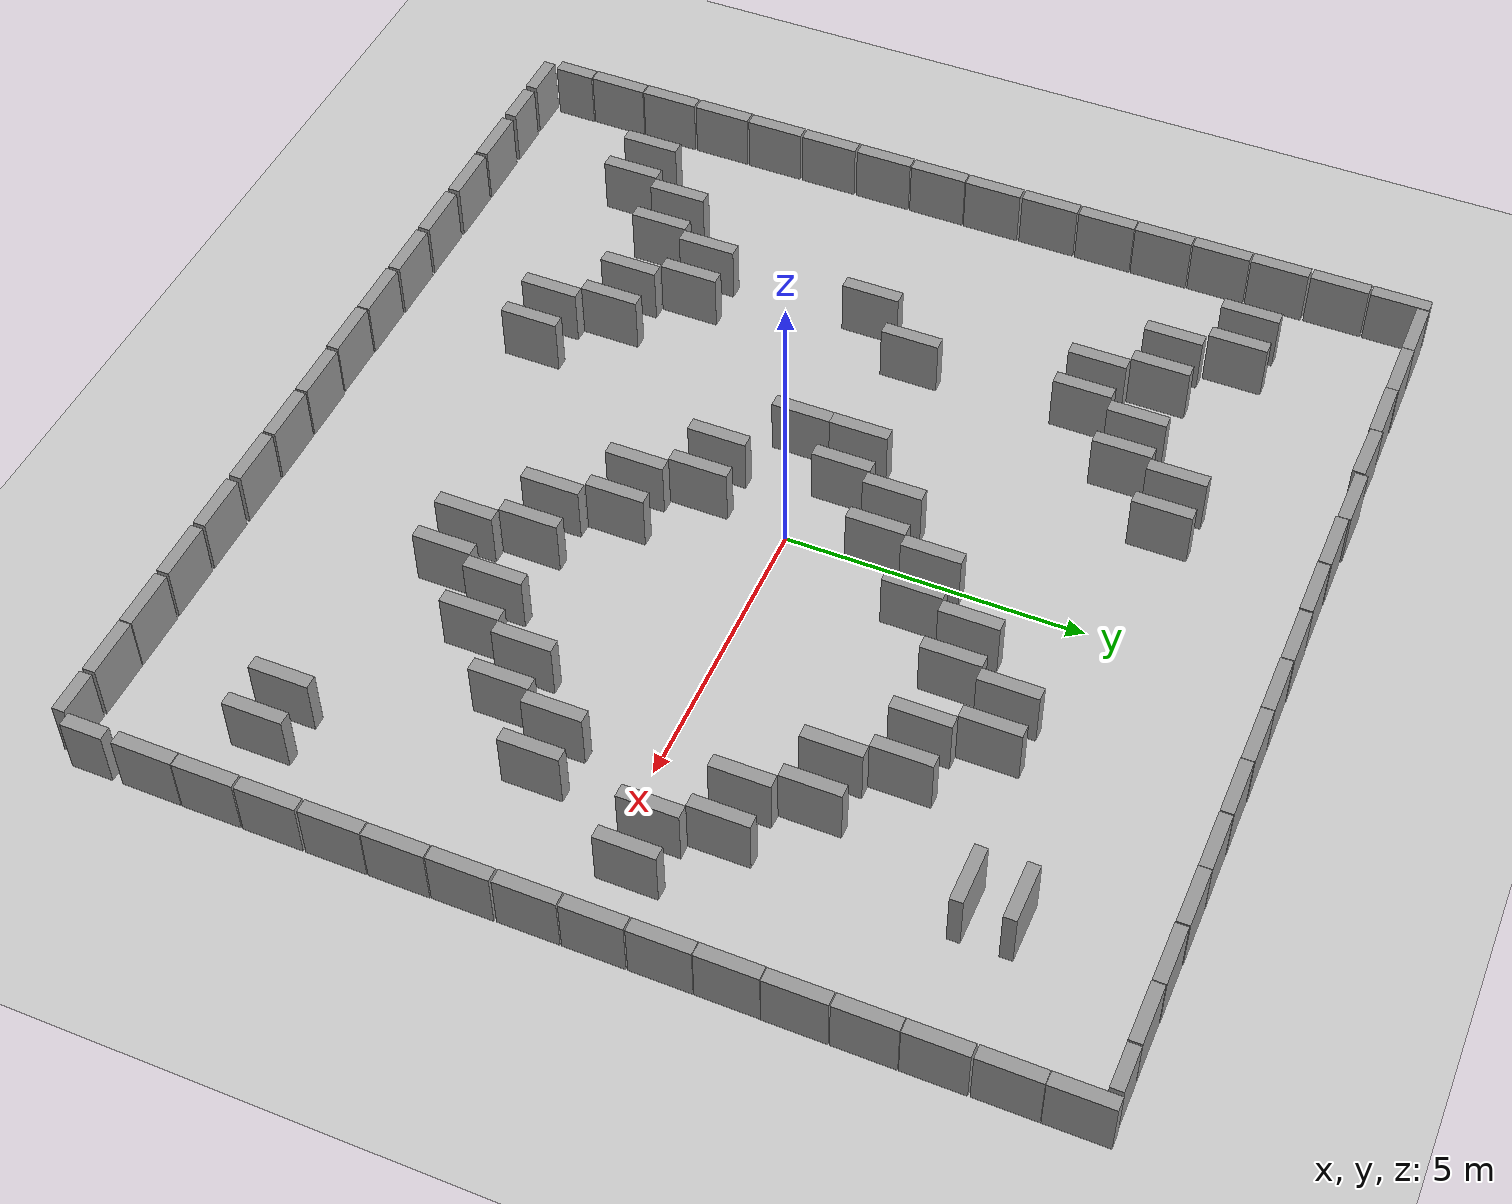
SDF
<sdf version="1.6">
 <world name="default">
  <light name="sun" type="directional">
   <pose>0 0 10 0 -0 0</pose>
   <diffuse>0.8 0.8 0.8 1</diffuse>
   <specular>0.1 0.1 0.1 1</specular>
   <attenuation>
    <range>1000</range>
    <constant>0.9</constant>
    <linear>0.01</linear>
    <quadratic>0.001</quadratic>
   </attenuation>
   <direction>-0.5 0.5 -1</direction>
  </light>
  <model name="ground_plane">
   <static>1</static>
   <static>1</static>
   <link name="link">
    <collision name="collision">
     <geometry><plane><normal>0 0 1</normal><size>100 100</size></plane></geometry>
     <surface><friction><ode><mu>100</mu><mu2>50</mu2></ode></friction></surface>
    </collision>
    <visual name="visual">
     <cast_shadows>0</cast_shadows>
     <geometry><plane><normal>0 0 1</normal><size>100 100</size></plane></geometry>
     <material>
      <script><uri>file://media/materials/scripts/gazebo.material</uri><name>Gazebo/Grey</name></script>
     </material>
    </visual>
   </link>
  </model>
  <gravity>0 0 -9.8</gravity>
  <magnetic_field>6e-06 2.3e-05 -4.2e-05</magnetic_field>
  <atmosphere type="adiabatic"/>
  <physics name="default_physics" default="0" type="ode">
   <max_step_size>0.001</max_step_size>
   <real_time_factor>1</real_time_factor>
   <real_time_update_rate>1000</real_time_update_rate>
  </physics>
  <scene><ambient>0.4 0.4 0.4 1</ambient><background>0.7 0.7 0.7 1</background><shadows>1</shadows></scene>
  <spherical_coordinates>
   <surface_model>EARTH_WGS84</surface_model>
   <latitude_deg>0</latitude_deg>
   <longitude_deg>0</longitude_deg>
   <elevation>0</elevation>
   <heading_deg>0</heading_deg>
  </spherical_coordinates>
  <audio><device>default</device></audio>
  <model name="unit_box_clone">
   <pose>-7.49845 8.11989 0.5 0 -0 0.00017</pose>
   <link name="link">
    <inertial>
     <mass>1</mass>
     <inertia>
      <ixx>0.166667</ixx>
      <ixy>0</ixy>
      <ixz>0</ixz>
      <iyy>0.166667</iyy>
      <iyz>0</iyz>
      <izz>0.166667</izz>
     </inertia>
    </inertial>
    <collision name="collision"><geometry><box><size>1 0.210541 1</size></box></geometry></collision>
    <visual name="visual">
     <geometry><box><size>1 0.210541 1</size></box></geometry>
     <material>
      <script><name>Gazebo/Grey</name><uri>file://media/materials/scripts/gazebo.material</uri></script>
     </material>
    </visual>
   </link>
  </model>
  <model name="unit_box_clone_0">
   <pose>-6.4973 8.11974 0.5 -0 -0 -0.002434</pose>
   <link name="link">
    <inertial>
     <mass>1</mass>
     <inertia>
      <ixx>0.166667</ixx>
      <ixy>0</ixy>
      <ixz>0</ixz>
      <iyy>0.166667</iyy>
      <iyz>0</iyz>
      <izz>0.166667</izz>
     </inertia>
    </inertial>
    <collision name="collision"><geometry><box><size>1 0.210541 1</size></box></geometry></collision>
    <visual name="visual">
     <geometry><box><size>1 0.210541 1</size></box></geometry>
     <material>
      <script><name>Gazebo/Grey</name><uri>file://media/materials/scripts/gazebo.material</uri></script>
     </material>
    </visual>
   </link>
  </model>
  <model name="unit_box_clone_1">
   <pose>-5.49732 8.10849 0.5 -0 -0 -0.002426</pose>
   <link name="link">
    <inertial>
     <mass>1</mass>
     <inertia>
      <ixx>0.166667</ixx>
      <ixy>0</ixy>
      <ixz>0</ixz>
      <iyy>0.166667</iyy>
      <iyz>0</iyz>
      <izz>0.166667</izz>
     </inertia>
    </inertial>
    <collision name="collision"><geometry><box><size>1 0.210541 1</size></box></geometry></collision>
    <visual name="visual">
     <geometry><box><size>1 0.210541 1</size></box></geometry>
     <material>
      <script><name>Gazebo/Grey</name><uri>file://media/materials/scripts/gazebo.material</uri></script>
     </material>
    </visual>
   </link>
  </model>
  <model name="unit_box_clone_2">
   <pose>-4.49485 8.11058 0.499999 1e-06 -2e-06 -0.026985</pose>
   <link name="link">
    <inertial>
     <mass>1</mass>
     <inertia>
      <ixx>0.166667</ixx>
      <ixy>0</ixy>
      <ixz>0</ixz>
      <iyy>0.166667</iyy>
      <iyz>0</iyz>
      <izz>0.166667</izz>
     </inertia>
    </inertial>
    <collision name="collision"><geometry><box><size>1 0.210541 1</size></box></geometry></collision>
    <visual name="visual">
     <geometry><box><size>1 0.210541 1</size></box></geometry>
     <material>
      <script><name>Gazebo/Grey</name><uri>file://media/materials/scripts/gazebo.material</uri></script>
     </material>
    </visual>
   </link>
  </model>
  <model name="unit_box_clone_3">
   <pose>-3.46835 8.15023 0.5 -0 -0 -0.007814</pose>
   <link name="link">
    <inertial>
     <mass>1</mass>
     <inertia>
      <ixx>0.166667</ixx>
      <ixy>0</ixy>
      <ixz>0</ixz>
      <iyy>0.166667</iyy>
      <iyz>0</iyz>
      <izz>0.166667</izz>
     </inertia>
    </inertial>
    <collision name="collision"><geometry><box><size>1 0.210541 1</size></box></geometry></collision>
    <visual name="visual">
     <geometry><box><size>1 0.210541 1</size></box></geometry>
     <material>
      <script><name>Gazebo/Grey</name><uri>file://media/materials/scripts/gazebo.material</uri></script>
     </material>
    </visual>
   </link>
  </model>
  <model name="unit_box_clone_4">
   <pose>-2.46316 8.11857 0.5 0 -0 0.00017</pose>
   <link name="link">
    <inertial>
     <mass>1</mass>
     <inertia>
      <ixx>0.166667</ixx>
      <ixy>0</ixy>
      <ixz>0</ixz>
      <iyy>0.166667</iyy>
      <iyz>0</iyz>
      <izz>0.166667</izz>
     </inertia>
    </inertial>
    <collision name="collision"><geometry><box><size>1 0.210541 1</size></box></geometry></collision>
    <visual name="visual">
     <geometry><box><size>1 0.210541 1</size></box></geometry>
     <material>
      <script><name>Gazebo/Grey</name><uri>file://media/materials/scripts/gazebo.material</uri></script>
     </material>
    </visual>
   </link>
  </model>
  <model name="unit_box_clone_5">
   <pose>-1.44425 8.11191 0.5 0 -0 0.00017</pose>
   <link name="link">
    <inertial>
     <mass>1</mass>
     <inertia>
      <ixx>0.166667</ixx>
      <ixy>0</ixy>
      <ixz>0</ixz>
      <iyy>0.166667</iyy>
      <iyz>0</iyz>
      <izz>0.166667</izz>
     </inertia>
    </inertial>
    <collision name="collision"><geometry><box><size>1 0.210541 1</size></box></geometry></collision>
    <visual name="visual">
     <geometry><box><size>1 0.210541 1</size></box></geometry>
     <material>
      <script><name>Gazebo/Grey</name><uri>file://media/materials/scripts/gazebo.material</uri></script>
     </material>
    </visual>
   </link>
  </model>
  <model name="unit_box_clone_6">
   <pose>-0.418683 8.11857 0.5 0 -0 0.00017</pose>
   <link name="link">
    <inertial>
     <mass>1</mass>
     <inertia>
      <ixx>0.166667</ixx>
      <ixy>0</ixy>
      <ixz>0</ixz>
      <iyy>0.166667</iyy>
      <iyz>0</iyz>
      <izz>0.166667</izz>
     </inertia>
    </inertial>
    <collision name="collision"><geometry><box><size>1 0.210541 1</size></box></geometry></collision>
    <visual name="visual">
     <geometry><box><size>1 0.210541 1</size></box></geometry>
     <material>
      <script><name>Gazebo/Grey</name><uri>file://media/materials/scripts/gazebo.material</uri></script>
     </material>
    </visual>
   </link>
  </model>
  <model name="unit_box_clone_7">
   <pose>0.592836 8.11144 0.5 0 -0 0.00017</pose>
   <link name="link">
    <inertial>
     <mass>1</mass>
     <inertia>
      <ixx>0.166667</ixx>
      <ixy>0</ixy>
      <ixz>0</ixz>
      <iyy>0.166667</iyy>
      <iyz>0</iyz>
      <izz>0.166667</izz>
     </inertia>
    </inertial>
    <collision name="collision"><geometry><box><size>1 0.210541 1</size></box></geometry></collision>
    <visual name="visual">
     <geometry><box><size>1 0.210541 1</size></box></geometry>
     <material>
      <script><name>Gazebo/Grey</name><uri>file://media/materials/scripts/gazebo.material</uri></script>
     </material>
    </visual>
   </link>
  </model>
  <model name="unit_box_clone_8">
   <pose>1.60043 8.10994 0.5 0 -0 0.00017</pose>
   <link name="link">
    <inertial>
     <mass>1</mass>
     <inertia>
      <ixx>0.166667</ixx>
      <ixy>0</ixy>
      <ixz>0</ixz>
      <iyy>0.166667</iyy>
      <iyz>0</iyz>
      <izz>0.166667</izz>
     </inertia>
    </inertial>
    <collision name="collision"><geometry><box><size>1 0.210541 1</size></box></geometry></collision>
    <visual name="visual">
     <geometry><box><size>1 0.210541 1</size></box></geometry>
     <material>
      <script><name>Gazebo/Grey</name><uri>file://media/materials/scripts/gazebo.material</uri></script>
     </material>
    </visual>
   </link>
  </model>
  <model name="unit_box_clone_9">
   <pose>2.60987 8.10276 0.5 0 -0 0.00017</pose>
   <link name="link">
    <inertial>
     <mass>1</mass>
     <inertia>
      <ixx>0.166667</ixx>
      <ixy>0</ixy>
      <ixz>0</ixz>
      <iyy>0.166667</iyy>
      <iyz>0</iyz>
      <izz>0.166667</izz>
     </inertia>
    </inertial>
    <collision name="collision"><geometry><box><size>1 0.210541 1</size></box></geometry></collision>
    <visual name="visual">
     <geometry><box><size>1 0.210541 1</size></box></geometry>
     <material>
      <script><name>Gazebo/Grey</name><uri>file://media/materials/scripts/gazebo.material</uri></script>
     </material>
    </visual>
   </link>
  </model>
  <model name="unit_box_clone_10">
   <pose>3.62649 8.09916 0.5 0 -0 0.00017</pose>
   <link name="link">
    <inertial>
     <mass>1</mass>
     <inertia>
      <ixx>0.166667</ixx>
      <ixy>0</ixy>
      <ixz>0</ixz>
      <iyy>0.166667</iyy>
      <iyz>0</iyz>
      <izz>0.166667</izz>
     </inertia>
    </inertial>
    <collision name="collision"><geometry><box><size>1 0.210541 1</size></box></geometry></collision>
    <visual name="visual">
     <geometry><box><size>1 0.210541 1</size></box></geometry>
     <material>
      <script><name>Gazebo/Grey</name><uri>file://media/materials/scripts/gazebo.material</uri></script>
     </material>
    </visual>
   </link>
  </model>
  <model name="unit_box_clone_11">
   <pose>4.63308 8.09534 0.5 0 0 -0.003388</pose>
   <link name="link">
    <inertial>
     <mass>1</mass>
     <inertia>
      <ixx>0.166667</ixx>
      <ixy>0</ixy>
      <ixz>0</ixz>
      <iyy>0.166667</iyy>
      <iyz>0</iyz>
      <izz>0.166667</izz>
     </inertia>
    </inertial>
    <collision name="collision"><geometry><box><size>1 0.210541 1</size></box></geometry></collision>
    <visual name="visual">
     <geometry><box><size>1 0.210541 1</size></box></geometry>
     <material>
      <script><name>Gazebo/Grey</name><uri>file://media/materials/scripts/gazebo.material</uri></script>
     </material>
    </visual>
   </link>
  </model>
  <model name="unit_box_0_clone_0">
   <pose>8.11522 6.68458 0.5 0 0 -0.000325</pose>
   <link name="link">
    <inertial>
     <mass>1</mass>
     <inertia>
      <ixx>0.166667</ixx>
      <ixy>0</ixy>
      <ixz>0</ixz>
      <iyy>0.166667</iyy>
      <iyz>0</iyz>
      <izz>0.166667</izz>
     </inertia>
    </inertial>
    <collision name="collision"><geometry><box><size>0.230819 1 1</size></box></geometry></collision>
    <visual name="visual">
     <geometry><box><size>0.230819 1 1</size></box></geometry>
     <material>
      <script><name>Gazebo/Grey</name><uri>file://media/materials/scripts/gazebo.material</uri></script>
     </material>
    </visual>
   </link>
  </model>
  <model name="unit_box_0_clone_1">
   <pose>8.11915 5.6517 0.5 0 -0 0.000224</pose>
   <link name="link">
    <inertial>
     <mass>1</mass>
     <inertia>
      <ixx>0.166667</ixx>
      <ixy>0</ixy>
      <ixz>0</ixz>
      <iyy>0.166667</iyy>
      <iyz>0</iyz>
      <izz>0.166667</izz>
     </inertia>
    </inertial>
    <collision name="collision"><geometry><box><size>0.230819 1 1</size></box></geometry></collision>
    <visual name="visual">
     <geometry><box><size>0.230819 1 1</size></box></geometry>
     <material>
      <script><name>Gazebo/Grey</name><uri>file://media/materials/scripts/gazebo.material</uri></script>
     </material>
    </visual>
   </link>
  </model>
  <model name="unit_box_0_clone_2">
   <pose>8.11914 4.64016 0.5 0 -0 0.000318</pose>
   <link name="link">
    <inertial>
     <mass>1</mass>
     <inertia>
      <ixx>0.166667</ixx>
      <ixy>0</ixy>
      <ixz>0</ixz>
      <iyy>0.166667</iyy>
      <iyz>0</iyz>
      <izz>0.166667</izz>
     </inertia>
    </inertial>
    <collision name="collision"><geometry><box><size>0.230819 1 1</size></box></geometry></collision>
    <visual name="visual">
     <geometry><box><size>0.230819 1 1</size></box></geometry>
     <material>
      <script><name>Gazebo/Grey</name><uri>file://media/materials/scripts/gazebo.material</uri></script>
     </material>
    </visual>
   </link>
  </model>
  <model name="unit_box_0_clone_3">
   <pose>8.11914 3.62228 0.5 0 -0 0.000299</pose>
   <link name="link">
    <inertial>
     <mass>1</mass>
     <inertia>
      <ixx>0.166667</ixx>
      <ixy>0</ixy>
      <ixz>0</ixz>
      <iyy>0.166667</iyy>
      <iyz>0</iyz>
      <izz>0.166667</izz>
     </inertia>
    </inertial>
    <collision name="collision"><geometry><box><size>0.230819 1 1</size></box></geometry></collision>
    <visual name="visual">
     <geometry><box><size>0.230819 1 1</size></box></geometry>
     <material>
      <script><name>Gazebo/Grey</name><uri>file://media/materials/scripts/gazebo.material</uri></script>
     </material>
    </visual>
   </link>
  </model>
  <model name="unit_box_0_clone_4">
   <pose>8.11332 2.61063 0.5 -0 -0 -0.000934</pose>
   <link name="link">
    <inertial>
     <mass>1</mass>
     <inertia>
      <ixx>0.166667</ixx>
      <ixy>0</ixy>
      <ixz>0</ixz>
      <iyy>0.166667</iyy>
      <iyz>0</iyz>
      <izz>0.166667</izz>
     </inertia>
    </inertial>
    <collision name="collision"><geometry><box><size>0.230819 1 1</size></box></geometry></collision>
    <visual name="visual">
     <geometry><box><size>0.230819 1 1</size></box></geometry>
     <material>
      <script><name>Gazebo/Grey</name><uri>file://media/materials/scripts/gazebo.material</uri></script>
     </material>
    </visual>
   </link>
  </model>
  <model name="unit_box_0_clone_5">
   <pose>8.11277 1.59919 0.5 0 -0 0.000299</pose>
   <link name="link">
    <inertial>
     <mass>1</mass>
     <inertia>
      <ixx>0.166667</ixx>
      <ixy>0</ixy>
      <ixz>0</ixz>
      <iyy>0.166667</iyy>
      <iyz>0</iyz>
      <izz>0.166667</izz>
     </inertia>
    </inertial>
    <collision name="collision"><geometry><box><size>0.230819 1 1</size></box></geometry></collision>
    <visual name="visual">
     <geometry><box><size>0.230819 1 1</size></box></geometry>
     <material>
      <script><name>Gazebo/Grey</name><uri>file://media/materials/scripts/gazebo.material</uri></script>
     </material>
    </visual>
   </link>
  </model>
  <model name="unit_box_0_clone_6">
   <pose>8.11277 0.574938 0.5 0 -0 0.000299</pose>
   <link name="link">
    <inertial>
     <mass>1</mass>
     <inertia>
      <ixx>0.166667</ixx>
      <ixy>0</ixy>
      <ixz>0</ixz>
      <iyy>0.166667</iyy>
      <iyz>0</iyz>
      <izz>0.166667</izz>
     </inertia>
    </inertial>
    <collision name="collision"><geometry><box><size>0.230819 1 1</size></box></geometry></collision>
    <visual name="visual">
     <geometry><box><size>0.230819 1 1</size></box></geometry>
     <material>
      <script><name>Gazebo/Grey</name><uri>file://media/materials/scripts/gazebo.material</uri></script>
     </material>
    </visual>
   </link>
  </model>
  <model name="unit_box_0_clone_7">
   <pose>8.11276 -0.44932 0.5 0 -0 0.000299</pose>
   <link name="link">
    <inertial>
     <mass>1</mass>
     <inertia>
      <ixx>0.166667</ixx>
      <ixy>0</ixy>
      <ixz>0</ixz>
      <iyy>0.166667</iyy>
      <iyz>0</iyz>
      <izz>0.166667</izz>
     </inertia>
    </inertial>
    <collision name="collision"><geometry><box><size>0.230819 1 1</size></box></geometry></collision>
    <visual name="visual">
     <geometry><box><size>0.230819 1 1</size></box></geometry>
     <material>
      <script><name>Gazebo/Grey</name><uri>file://media/materials/scripts/gazebo.material</uri></script>
     </material>
    </visual>
   </link>
  </model>
  <model name="unit_box_0_clone_8">
   <pose>8.11912 -1.48629 0.5 0 -0 0.000299</pose>
   <link name="link">
    <inertial>
     <mass>1</mass>
     <inertia>
      <ixx>0.166667</ixx>
      <ixy>0</ixy>
      <ixz>0</ixz>
      <iyy>0.166667</iyy>
      <iyz>0</iyz>
      <izz>0.166667</izz>
     </inertia>
    </inertial>
    <collision name="collision"><geometry><box><size>0.230819 1 1</size></box></geometry></collision>
    <visual name="visual">
     <geometry><box><size>0.230819 1 1</size></box></geometry>
     <material>
      <script><name>Gazebo/Grey</name><uri>file://media/materials/scripts/gazebo.material</uri></script>
     </material>
    </visual>
   </link>
  </model>
  <model name="unit_box_0_clone_9">
   <pose>8.12548 -2.5042 0.5 0 -0 0.000299</pose>
   <link name="link">
    <inertial>
     <mass>1</mass>
     <inertia>
      <ixx>0.166667</ixx>
      <ixy>0</ixy>
      <ixz>0</ixz>
      <iyy>0.166667</iyy>
      <iyz>0</iyz>
      <izz>0.166667</izz>
     </inertia>
    </inertial>
    <collision name="collision"><geometry><box><size>0.230819 1 1</size></box></geometry></collision>
    <visual name="visual">
     <geometry><box><size>0.230819 1 1</size></box></geometry>
     <material>
      <script><name>Gazebo/Grey</name><uri>file://media/materials/scripts/gazebo.material</uri></script>
     </material>
    </visual>
   </link>
  </model>
  <model name="unit_box_0_clone_10">
   <pose>8.12331 -3.52223 0.5 0 -0 0.000299</pose>
   <link name="link">
    <inertial>
     <mass>1</mass>
     <inertia>
      <ixx>0.166667</ixx>
      <ixy>0</ixy>
      <ixz>0</ixz>
      <iyy>0.166667</iyy>
      <iyz>0</iyz>
      <izz>0.166667</izz>
     </inertia>
    </inertial>
    <collision name="collision"><geometry><box><size>0.230819 1 1</size></box></geometry></collision>
    <visual name="visual">
     <geometry><box><size>0.230819 1 1</size></box></geometry>
     <material>
      <script><name>Gazebo/Grey</name><uri>file://media/materials/scripts/gazebo.material</uri></script>
     </material>
    </visual>
   </link>
  </model>
  <model name="unit_box_0_clone_11">
   <pose>8.1233 -4.56316 0.5 0 -0 0.000299</pose>
   <link name="link">
    <inertial>
     <mass>1</mass>
     <inertia>
      <ixx>0.166667</ixx>
      <ixy>0</ixy>
      <ixz>0</ixz>
      <iyy>0.166667</iyy>
      <iyz>0</iyz>
      <izz>0.166667</izz>
     </inertia>
    </inertial>
    <collision name="collision"><geometry><box><size>0.230819 1 1</size></box></geometry></collision>
    <visual name="visual">
     <geometry><box><size>0.230819 1 1</size></box></geometry>
     <material>
      <script><name>Gazebo/Grey</name><uri>file://media/materials/scripts/gazebo.material</uri></script>
     </material>
    </visual>
   </link>
  </model>
  <model name="unit_box_0_clone_12">
   <pose>8.11815 -5.59377 0.5 0 -0 0.000299</pose>
   <link name="link">
    <inertial>
     <mass>1</mass>
     <inertia>
      <ixx>0.166667</ixx>
      <ixy>0</ixy>
      <ixz>0</ixz>
      <iyy>0.166667</iyy>
      <iyz>0</iyz>
      <izz>0.166667</izz>
     </inertia>
    </inertial>
    <collision name="collision"><geometry><box><size>0.230819 1 1</size></box></geometry></collision>
    <visual name="visual">
     <geometry><box><size>0.230819 1 1</size></box></geometry>
     <material>
      <script><name>Gazebo/Grey</name><uri>file://media/materials/scripts/gazebo.material</uri></script>
     </material>
    </visual>
   </link>
  </model>
  <model name="unit_box_0_clone_13">
   <pose>8.11333 -6.60776 0.5 -0 -0 -0.005308</pose>
   <link name="link">
    <inertial>
     <mass>1</mass>
     <inertia>
      <ixx>0.166667</ixx>
      <ixy>0</ixy>
      <ixz>0</ixz>
      <iyy>0.166667</iyy>
      <iyz>0</iyz>
      <izz>0.166667</izz>
     </inertia>
    </inertial>
    <collision name="collision"><geometry><box><size>0.230819 1 1</size></box></geometry></collision>
    <visual name="visual">
     <geometry><box><size>0.230819 1 1</size></box></geometry>
     <material>
      <script><name>Gazebo/Grey</name><uri>file://media/materials/scripts/gazebo.material</uri></script>
     </material>
    </visual>
   </link>
  </model>
  <model name="unit_box_clone_15_clone_0">
   <pose>6.71207 -8.13115 0.5 0 -0 0.00017</pose>
   <link name="link">
    <inertial>
     <mass>1</mass>
     <inertia>
      <ixx>0.166667</ixx>
      <ixy>0</ixy>
      <ixz>0</ixz>
      <iyy>0.166667</iyy>
      <iyz>0</iyz>
      <izz>0.166667</izz>
     </inertia>
    </inertial>
    <collision name="collision"><geometry><box><size>1 0.210541 1</size></box></geometry></collision>
    <visual name="visual">
     <geometry><box><size>1 0.210541 1</size></box></geometry>
     <material>
      <script><name>Gazebo/Grey</name><uri>file://media/materials/scripts/gazebo.material</uri></script>
     </material>
    </visual>
   </link>
  </model>
  <model name="unit_box_clone_15_clone_1">
   <pose>5.69715 -8.13115 0.5 0 -0 0.00017</pose>
   <link name="link">
    <inertial>
     <mass>1</mass>
     <inertia>
      <ixx>0.166667</ixx>
      <ixy>0</ixy>
      <ixz>0</ixz>
      <iyy>0.166667</iyy>
      <iyz>0</iyz>
      <izz>0.166667</izz>
     </inertia>
    </inertial>
    <collision name="collision"><geometry><box><size>1 0.210541 1</size></box></geometry></collision>
    <visual name="visual">
     <geometry><box><size>1 0.210541 1</size></box></geometry>
     <material>
      <script><name>Gazebo/Grey</name><uri>file://media/materials/scripts/gazebo.material</uri></script>
     </material>
    </visual>
   </link>
  </model>
  <model name="unit_box_clone_15_clone_2">
   <pose>4.63881 -8.13733 0.5 0 -0 0.00017</pose>
   <link name="link">
    <inertial>
     <mass>1</mass>
     <inertia>
      <ixx>0.166667</ixx>
      <ixy>0</ixy>
      <ixz>0</ixz>
      <iyy>0.166667</iyy>
      <iyz>0</iyz>
      <izz>0.166667</izz>
     </inertia>
    </inertial>
    <collision name="collision"><geometry><box><size>1 0.210541 1</size></box></geometry></collision>
    <visual name="visual">
     <geometry><box><size>1 0.210541 1</size></box></geometry>
     <material>
      <script><name>Gazebo/Grey</name><uri>file://media/materials/scripts/gazebo.material</uri></script>
     </material>
    </visual>
   </link>
  </model>
  <model name="unit_box_clone_15_clone_3">
   <pose>3.57975 -8.13733 0.5 0 -0 0.00017</pose>
   <link name="link">
    <inertial>
     <mass>1</mass>
     <inertia>
      <ixx>0.166667</ixx>
      <ixy>0</ixy>
      <ixz>0</ixz>
      <iyy>0.166667</iyy>
      <iyz>0</iyz>
      <izz>0.166667</izz>
     </inertia>
    </inertial>
    <collision name="collision"><geometry><box><size>1 0.210541 1</size></box></geometry></collision>
    <visual name="visual">
     <geometry><box><size>1 0.210541 1</size></box></geometry>
     <material>
      <script><name>Gazebo/Grey</name><uri>file://media/materials/scripts/gazebo.material</uri></script>
     </material>
    </visual>
   </link>
  </model>
  <model name="unit_box_clone_15_clone_4">
   <pose>2.49815 -8.13731 0.5 0 -0 0.00017</pose>
   <link name="link">
    <inertial>
     <mass>1</mass>
     <inertia>
      <ixx>0.166667</ixx>
      <ixy>0</ixy>
      <ixz>0</ixz>
      <iyy>0.166667</iyy>
      <iyz>0</iyz>
      <izz>0.166667</izz>
     </inertia>
    </inertial>
    <collision name="collision"><geometry><box><size>1 0.210541 1</size></box></geometry></collision>
    <visual name="visual">
     <geometry><box><size>1 0.210541 1</size></box></geometry>
     <material>
      <script><name>Gazebo/Grey</name><uri>file://media/materials/scripts/gazebo.material</uri></script>
     </material>
    </visual>
   </link>
  </model>
  <model name="unit_box_clone_15_clone_5">
   <pose>1.46162 -8.12604 0.5 0 -0 0.00017</pose>
   <link name="link">
    <inertial>
     <mass>1</mass>
     <inertia>
      <ixx>0.166667</ixx>
      <ixy>0</ixy>
      <ixz>0</ixz>
      <iyy>0.166667</iyy>
      <iyz>0</iyz>
      <izz>0.166667</izz>
     </inertia>
    </inertial>
    <collision name="collision"><geometry><box><size>1 0.210541 1</size></box></geometry></collision>
    <visual name="visual">
     <geometry><box><size>1 0.210541 1</size></box></geometry>
     <material>
      <script><name>Gazebo/Grey</name><uri>file://media/materials/scripts/gazebo.material</uri></script>
     </material>
    </visual>
   </link>
  </model>
  <model name="unit_box_clone_15_clone_6">
   <pose>0.425089 -8.12603 0.5 0 -0 0.00017</pose>
   <link name="link">
    <inertial>
     <mass>1</mass>
     <inertia>
      <ixx>0.166667</ixx>
      <ixy>0</ixy>
      <ixz>0</ixz>
      <iyy>0.166667</iyy>
      <iyz>0</iyz>
      <izz>0.166667</izz>
     </inertia>
    </inertial>
    <collision name="collision"><geometry><box><size>1 0.210541 1</size></box></geometry></collision>
    <visual name="visual">
     <geometry><box><size>1 0.210541 1</size></box></geometry>
     <material>
      <script><name>Gazebo/Grey</name><uri>file://media/materials/scripts/gazebo.material</uri></script>
     </material>
    </visual>
   </link>
  </model>
  <model name="unit_box_clone_15_clone_7">
   <pose>-0.633973 -8.14859 0.5 0 -0 0.00017</pose>
   <link name="link">
    <inertial>
     <mass>1</mass>
     <inertia>
      <ixx>0.166667</ixx>
      <ixy>0</ixy>
      <ixz>0</ixz>
      <iyy>0.166667</iyy>
      <iyz>0</iyz>
      <izz>0.166667</izz>
     </inertia>
    </inertial>
    <collision name="collision"><geometry><box><size>1 0.210541 1</size></box></geometry></collision>
    <visual name="visual">
     <geometry><box><size>1 0.210541 1</size></box></geometry>
     <material>
      <script><name>Gazebo/Grey</name><uri>file://media/materials/scripts/gazebo.material</uri></script>
     </material>
    </visual>
   </link>
  </model>
  <model name="unit_box_clone_15_clone_8">
   <pose>-1.65923 -8.1373 0.5 0 -0 0.00017</pose>
   <link name="link">
    <inertial>
     <mass>1</mass>
     <inertia>
      <ixx>0.166667</ixx>
      <ixy>0</ixy>
      <ixz>0</ixz>
      <iyy>0.166667</iyy>
      <iyz>0</iyz>
      <izz>0.166667</izz>
     </inertia>
    </inertial>
    <collision name="collision"><geometry><box><size>1 0.210541 1</size></box></geometry></collision>
    <visual name="visual">
     <geometry><box><size>1 0.210541 1</size></box></geometry>
     <material>
      <script><name>Gazebo/Grey</name><uri>file://media/materials/scripts/gazebo.material</uri></script>
     </material>
    </visual>
   </link>
  </model>
  <model name="unit_box_clone_15_clone_9">
   <pose>-2.70703 -8.12605 0.5 0 -0 0.00017</pose>
   <link name="link">
    <inertial>
     <mass>1</mass>
     <inertia>
      <ixx>0.166667</ixx>
      <ixy>0</ixy>
      <ixz>0</ixz>
      <iyy>0.166667</iyy>
      <iyz>0</iyz>
      <izz>0.166667</izz>
     </inertia>
    </inertial>
    <collision name="collision"><geometry><box><size>1 0.210541 1</size></box></geometry></collision>
    <visual name="visual">
     <geometry><box><size>1 0.210541 1</size></box></geometry>
     <material>
      <script><name>Gazebo/Grey</name><uri>file://media/materials/scripts/gazebo.material</uri></script>
     </material>
    </visual>
   </link>
  </model>
  <model name="unit_box_clone_15_clone_10">
   <pose>-3.77736 -8.12604 0.5 0 -0 0.00017</pose>
   <link name="link">
    <inertial>
     <mass>1</mass>
     <inertia>
      <ixx>0.166667</ixx>
      <ixy>0</ixy>
      <ixz>0</ixz>
      <iyy>0.166667</iyy>
      <iyz>0</iyz>
      <izz>0.166667</izz>
     </inertia>
    </inertial>
    <collision name="collision"><geometry><box><size>1 0.210541 1</size></box></geometry></collision>
    <visual name="visual">
     <geometry><box><size>1 0.210541 1</size></box></geometry>
     <material>
      <script><name>Gazebo/Grey</name><uri>file://media/materials/scripts/gazebo.material</uri></script>
     </material>
    </visual>
   </link>
  </model>
  <model name="unit_box_clone_15_clone_11">
   <pose>-4.85896 -8.11478 0.5 0 -0 0.00017</pose>
   <link name="link">
    <inertial>
     <mass>1</mass>
     <inertia>
      <ixx>0.166667</ixx>
      <ixy>0</ixy>
      <ixz>0</ixz>
      <iyy>0.166667</iyy>
      <iyz>0</iyz>
      <izz>0.166667</izz>
     </inertia>
    </inertial>
    <collision name="collision"><geometry><box><size>1 0.210541 1</size></box></geometry></collision>
    <visual name="visual">
     <geometry><box><size>1 0.210541 1</size></box></geometry>
     <material>
      <script><name>Gazebo/Grey</name><uri>file://media/materials/scripts/gazebo.material</uri></script>
     </material>
    </visual>
   </link>
  </model>
  <model name="unit_box_clone_15_clone_12">
   <pose>-5.91802 -8.11477 0.5 0 -0 0.00017</pose>
   <link name="link">
    <inertial>
     <mass>1</mass>
     <inertia>
      <ixx>0.166667</ixx>
      <ixy>0</ixy>
      <ixz>0</ixz>
      <iyy>0.166667</iyy>
      <iyz>0</iyz>
      <izz>0.166667</izz>
     </inertia>
    </inertial>
    <collision name="collision"><geometry><box><size>1 0.210541 1</size></box></geometry></collision>
    <visual name="visual">
     <geometry><box><size>1 0.210541 1</size></box></geometry>
     <material>
      <script><name>Gazebo/Grey</name><uri>file://media/materials/scripts/gazebo.material</uri></script>
     </material>
    </visual>
   </link>
  </model>
  <model name="unit_box_0_clone_4_clone">
   <pose>-8.12647 7.71769 0.5 0 -0 0.000299</pose>
   <link name="link">
    <inertial>
     <mass>1</mass>
     <inertia>
      <ixx>0.166667</ixx>
      <ixy>0</ixy>
      <ixz>0</ixz>
      <iyy>0.166667</iyy>
      <iyz>0</iyz>
      <izz>0.166667</izz>
     </inertia>
    </inertial>
    <collision name="collision"><geometry><box><size>0.230819 1 1</size></box></geometry></collision>
    <visual name="visual">
     <geometry><box><size>0.230819 1 1</size></box></geometry>
     <material>
      <script><name>Gazebo/Grey</name><uri>file://media/materials/scripts/gazebo.material</uri></script>
     </material>
    </visual>
   </link>
  </model>
  <model name="unit_box_0_clone_4_clone_0">
   <pose>-8.13281 6.68715 0.5 0 -0 0.000299</pose>
   <link name="link">
    <inertial>
     <mass>1</mass>
     <inertia>
      <ixx>0.166667</ixx>
      <ixy>0</ixy>
      <ixz>0</ixz>
      <iyy>0.166667</iyy>
      <iyz>0</iyz>
      <izz>0.166667</izz>
     </inertia>
    </inertial>
    <collision name="collision"><geometry><box><size>0.230819 1 1</size></box></geometry></collision>
    <visual name="visual">
     <geometry><box><size>0.230819 1 1</size></box></geometry>
     <material>
      <script><name>Gazebo/Grey</name><uri>file://media/materials/scripts/gazebo.material</uri></script>
     </material>
    </visual>
   </link>
  </model>
  <model name="unit_box_0_clone_4_clone_1">
   <pose>-8.12606 5.64722 0.5 0 -0 0.000299</pose>
   <link name="link">
    <inertial>
     <mass>1</mass>
     <inertia>
      <ixx>0.166667</ixx>
      <ixy>0</ixy>
      <ixz>0</ixz>
      <iyy>0.166667</iyy>
      <iyz>0</iyz>
      <izz>0.166667</izz>
     </inertia>
    </inertial>
    <collision name="collision"><geometry><box><size>0.230819 1 1</size></box></geometry></collision>
    <visual name="visual">
     <geometry><box><size>0.230819 1 1</size></box></geometry>
     <material>
      <script><name>Gazebo/Grey</name><uri>file://media/materials/scripts/gazebo.material</uri></script>
     </material>
    </visual>
   </link>
  </model>
  <model name="unit_box_0_clone_4_clone_2">
   <pose>-8.12607 4.6208 0.5 0 -0 0.000299</pose>
   <link name="link">
    <inertial>
     <mass>1</mass>
     <inertia>
      <ixx>0.166667</ixx>
      <ixy>0</ixy>
      <ixz>0</ixz>
      <iyy>0.166667</iyy>
      <iyz>0</iyz>
      <izz>0.166667</izz>
     </inertia>
    </inertial>
    <collision name="collision"><geometry><box><size>0.230819 1 1</size></box></geometry></collision>
    <visual name="visual">
     <geometry><box><size>0.230819 1 1</size></box></geometry>
     <material>
      <script><name>Gazebo/Grey</name><uri>file://media/materials/scripts/gazebo.material</uri></script>
     </material>
    </visual>
   </link>
  </model>
  <model name="unit_box_0_clone_4_clone_3">
   <pose>-8.11932 3.59437 0.5 0 -0 0.000299</pose>
   <link name="link">
    <inertial>
     <mass>1</mass>
     <inertia>
      <ixx>0.166667</ixx>
      <ixy>0</ixy>
      <ixz>0</ixz>
      <iyy>0.166667</iyy>
      <iyz>0</iyz>
      <izz>0.166667</izz>
     </inertia>
    </inertial>
    <collision name="collision"><geometry><box><size>0.230819 1 1</size></box></geometry></collision>
    <visual name="visual">
     <geometry><box><size>0.230819 1 1</size></box></geometry>
     <material>
      <script><name>Gazebo/Grey</name><uri>file://media/materials/scripts/gazebo.material</uri></script>
     </material>
    </visual>
   </link>
  </model>
  <model name="unit_box_0_clone_4_clone_4">
   <pose>-8.11932 2.57471 0.5 0 -0 0.000299</pose>
   <link name="link">
    <inertial>
     <mass>1</mass>
     <inertia>
      <ixx>0.166667</ixx>
      <ixy>0</ixy>
      <ixz>0</ixz>
      <iyy>0.166667</iyy>
      <iyz>0</iyz>
      <izz>0.166667</izz>
     </inertia>
    </inertial>
    <collision name="collision"><geometry><box><size>0.230819 1 1</size></box></geometry></collision>
    <visual name="visual">
     <geometry><box><size>0.230819 1 1</size></box></geometry>
     <material>
      <script><name>Gazebo/Grey</name><uri>file://media/materials/scripts/gazebo.material</uri></script>
     </material>
    </visual>
   </link>
  </model>
  <model name="unit_box_0_clone_4_clone_5">
   <pose>-8.12608 1.54157 0.5 0 -0 0.000299</pose>
   <link name="link">
    <inertial>
     <mass>1</mass>
     <inertia>
      <ixx>0.166667</ixx>
      <ixy>0</ixy>
      <ixz>0</ixz>
      <iyy>0.166667</iyy>
      <iyz>0</iyz>
      <izz>0.166667</izz>
     </inertia>
    </inertial>
    <collision name="collision"><geometry><box><size>0.230819 1 1</size></box></geometry></collision>
    <visual name="visual">
     <geometry><box><size>0.230819 1 1</size></box></geometry>
     <material>
      <script><name>Gazebo/Grey</name><uri>file://media/materials/scripts/gazebo.material</uri></script>
     </material>
    </visual>
   </link>
  </model>
  <model name="unit_box_0_clone_4_clone_6">
   <pose>-8.11933 0.50163 0.5 0 -0 0.000299</pose>
   <link name="link">
    <inertial>
     <mass>1</mass>
     <inertia>
      <ixx>0.166667</ixx>
      <ixy>0</ixy>
      <ixz>0</ixz>
      <iyy>0.166667</iyy>
      <iyz>0</iyz>
      <izz>0.166667</izz>
     </inertia>
    </inertial>
    <collision name="collision"><geometry><box><size>0.230819 1 1</size></box></geometry></collision>
    <visual name="visual">
     <geometry><box><size>0.230819 1 1</size></box></geometry>
     <material>
      <script><name>Gazebo/Grey</name><uri>file://media/materials/scripts/gazebo.material</uri></script>
     </material>
    </visual>
   </link>
  </model>
  <model name="unit_box_0_clone_4_clone_7">
   <pose>-8.12609 -0.518034 0.5 0 -0 0.000299</pose>
   <link name="link">
    <inertial>
     <mass>1</mass>
     <inertia>
      <ixx>0.166667</ixx>
      <ixy>0</ixy>
      <ixz>0</ixz>
      <iyy>0.166667</iyy>
      <iyz>0</iyz>
      <izz>0.166667</izz>
     </inertia>
    </inertial>
    <collision name="collision"><geometry><box><size>0.230819 1 1</size></box></geometry></collision>
    <visual name="visual">
     <geometry><box><size>0.230819 1 1</size></box></geometry>
     <material>
      <script><name>Gazebo/Grey</name><uri>file://media/materials/scripts/gazebo.material</uri></script>
     </material>
    </visual>
   </link>
  </model>
  <model name="unit_box_0_clone_4_clone_8">
   <pose>-8.13284 -1.54445 0.5 0 -0 0.000299</pose>
   <link name="link">
    <inertial>
     <mass>1</mass>
     <inertia>
      <ixx>0.166667</ixx>
      <ixy>0</ixy>
      <ixz>0</ixz>
      <iyy>0.166667</iyy>
      <iyz>0</iyz>
      <izz>0.166667</izz>
     </inertia>
    </inertial>
    <collision name="collision"><geometry><box><size>0.230819 1 1</size></box></geometry></collision>
    <visual name="visual">
     <geometry><box><size>0.230819 1 1</size></box></geometry>
     <material>
      <script><name>Gazebo/Grey</name><uri>file://media/materials/scripts/gazebo.material</uri></script>
     </material>
    </visual>
   </link>
  </model>
  <model name="unit_box_0_clone_4_clone_9">
   <pose>-8.13285 -2.58439 0.5 0 -0 0.000299</pose>
   <link name="link">
    <inertial>
     <mass>1</mass>
     <inertia>
      <ixx>0.166667</ixx>
      <ixy>0</ixy>
      <ixz>0</ixz>
      <iyy>0.166667</iyy>
      <iyz>0</iyz>
      <izz>0.166667</izz>
     </inertia>
    </inertial>
    <collision name="collision"><geometry><box><size>0.230819 1 1</size></box></geometry></collision>
    <visual name="visual">
     <geometry><box><size>0.230819 1 1</size></box></geometry>
     <material>
      <script><name>Gazebo/Grey</name><uri>file://media/materials/scripts/gazebo.material</uri></script>
     </material>
    </visual>
   </link>
  </model>
  <model name="unit_box_0_clone_4_clone_10">
   <pose>-8.13285 -3.62431 0.5 0 -0 0.000299</pose>
   <link name="link">
    <inertial>
     <mass>1</mass>
     <inertia>
      <ixx>0.166667</ixx>
      <ixy>0</ixy>
      <ixz>0</ixz>
      <iyy>0.166667</iyy>
      <iyz>0</iyz>
      <izz>0.166667</izz>
     </inertia>
    </inertial>
    <collision name="collision"><geometry><box><size>0.230819 1 1</size></box></geometry></collision>
    <visual name="visual">
     <geometry><box><size>0.230819 1 1</size></box></geometry>
     <material>
      <script><name>Gazebo/Grey</name><uri>file://media/materials/scripts/gazebo.material</uri></script>
     </material>
    </visual>
   </link>
  </model>
  <model name="unit_box_0_clone_4_clone_11">
   <pose>-8.1396 -4.65747 0.5 0 -0 0.000299</pose>
   <link name="link">
    <inertial>
     <mass>1</mass>
     <inertia>
      <ixx>0.166667</ixx>
      <ixy>0</ixy>
      <ixz>0</ixz>
      <iyy>0.166667</iyy>
      <iyz>0</iyz>
      <izz>0.166667</izz>
     </inertia>
    </inertial>
    <collision name="collision"><geometry><box><size>0.230819 1 1</size></box></geometry></collision>
    <visual name="visual">
     <geometry><box><size>0.230819 1 1</size></box></geometry>
     <material>
      <script><name>Gazebo/Grey</name><uri>file://media/materials/scripts/gazebo.material</uri></script>
     </material>
    </visual>
   </link>
  </model>
  <model name="unit_box_0_clone_4_clone_12">
   <pose>-8.1396 -5.69064 0.5 0 -0 0.000299</pose>
   <link name="link">
    <inertial>
     <mass>1</mass>
     <inertia>
      <ixx>0.166667</ixx>
      <ixy>0</ixy>
      <ixz>0</ixz>
      <iyy>0.166667</iyy>
      <iyz>0</iyz>
      <izz>0.166667</izz>
     </inertia>
    </inertial>
    <collision name="collision"><geometry><box><size>0.230819 1 1</size></box></geometry></collision>
    <visual name="visual">
     <geometry><box><size>0.230819 1 1</size></box></geometry>
     <material>
      <script><name>Gazebo/Grey</name><uri>file://media/materials/scripts/gazebo.material</uri></script>
     </material>
    </visual>
   </link>
  </model>
  <model name="unit_box_0_clone_4_clone_13">
   <pose>-8.14113 -6.70874 0.5 0 -0 -0.008563</pose>
   <link name="link">
    <inertial>
     <mass>1</mass>
     <inertia>
      <ixx>0.166667</ixx>
      <ixy>0</ixy>
      <ixz>0</ixz>
      <iyy>0.166667</iyy>
      <iyz>0</iyz>
      <izz>0.166667</izz>
     </inertia>
    </inertial>
    <collision name="collision"><geometry><box><size>0.230819 1 1</size></box></geometry></collision>
    <visual name="visual">
     <geometry><box><size>0.230819 1 1</size></box></geometry>
     <material>
      <script><name>Gazebo/Grey</name><uri>file://media/materials/scripts/gazebo.material</uri></script>
     </material>
    </visual>
   </link>
  </model>
  <model name="unit_box_0_clone_0_clone">
   <pose>8.11438 7.69322 0.5 0 -0 0.000206</pose>
   <link name="link">
    <inertial>
     <mass>1</mass>
     <inertia>
      <ixx>0.166667</ixx>
      <ixy>0</ixy>
      <ixz>0</ixz>
      <iyy>0.166667</iyy>
      <iyz>0</iyz>
      <izz>0.166667</izz>
     </inertia>
    </inertial>
    <collision name="collision"><geometry><box><size>0.230819 1 1</size></box></geometry></collision>
    <visual name="visual">
     <geometry><box><size>0.230819 1 1</size></box></geometry>
     <material>
      <script><name>Gazebo/Grey</name><uri>file://media/materials/scripts/gazebo.material</uri></script>
     </material>
    </visual>
   </link>
  </model>
  <model name="unit_box_clone_11_clone">
   <pose>5.6544 8.0837 0.5 0 -0 -0.00294</pose>
   <link name="link">
    <inertial>
     <mass>1</mass>
     <inertia>
      <ixx>0.166667</ixx>
      <ixy>0</ixy>
      <ixz>0</ixz>
      <iyy>0.166667</iyy>
      <iyz>0</iyz>
      <izz>0.166667</izz>
     </inertia>
    </inertial>
    <collision name="collision"><geometry><box><size>1 0.210541 1</size></box></geometry></collision>
    <visual name="visual">
     <geometry><box><size>1 0.210541 1</size></box></geometry>
     <material>
      <script><name>Gazebo/Grey</name><uri>file://media/materials/scripts/gazebo.material</uri></script>
     </material>
    </visual>
   </link>
  </model>
  <model name="unit_box_clone_11_clone_0">
   <pose>6.66438 8.07353 0.5 0 0 -0.00331</pose>
   <link name="link">
    <inertial>
     <mass>1</mass>
     <inertia>
      <ixx>0.166667</ixx>
      <ixy>0</ixy>
      <ixz>0</ixz>
      <iyy>0.166667</iyy>
      <iyz>0</iyz>
      <izz>0.166667</izz>
     </inertia>
    </inertial>
    <collision name="collision"><geometry><box><size>1 0.210541 1</size></box></geometry></collision>
    <visual name="visual">
     <geometry><box><size>1 0.210541 1</size></box></geometry>
     <material>
      <script><name>Gazebo/Grey</name><uri>file://media/materials/scripts/gazebo.material</uri></script>
     </material>
    </visual>
   </link>
  </model>
  <model name="unit_box_clone_11_clone_1_clone">
   <pose>7.56439 8.07325 0.499997 1e-06 8e-06 -0.00323</pose>
   <link name="link">
    <inertial>
     <mass>1</mass>
     <inertia>
      <ixx>0.166667</ixx>
      <ixy>0</ixy>
      <ixz>0</ixz>
      <iyy>0.166667</iyy>
      <iyz>0</iyz>
      <izz>0.166667</izz>
     </inertia>
    </inertial>
    <collision name="collision"><geometry><box><size>0.750223 0.210541 1</size></box></geometry></collision>
    <visual name="visual">
     <geometry><box><size>0.750223 0.210541 1</size></box></geometry>
     <material>
      <script><name>Gazebo/Grey</name><uri>file://media/materials/scripts/gazebo.material</uri></script>
     </material>
    </visual>
   </link>
  </model>
  <model name="unit_box_clone_11_clone_1_clone_0">
   <pose>-6.9088 -8.11956 0.500001 0 2e-06 0.001231</pose>
   <link name="link">
    <inertial>
     <mass>1</mass>
     <inertia>
      <ixx>0.166667</ixx>
      <ixy>0</ixy>
      <ixz>0</ixz>
      <iyy>0.166667</iyy>
      <iyz>0</iyz>
      <izz>0.166667</izz>
     </inertia>
    </inertial>
    <collision name="collision"><geometry><box><size>0.750223 0.210541 1</size></box></geometry></collision>
    <visual name="visual">
     <geometry><box><size>0.750223 0.210541 1</size></box></geometry>
     <material>
      <script><name>Gazebo/Grey</name><uri>file://media/materials/scripts/gazebo.material</uri></script>
     </material>
    </visual>
   </link>
  </model>
  <model name="unit_box_0_clone_4_clone_13_clone_clone">
   <pose>-8.13833 -7.5766 0.500001 -1e-06 -2e-06 -0.015808</pose>
   <link name="link">
    <inertial>
     <mass>1</mass>
     <inertia>
      <ixx>0.166667</ixx>
      <ixy>0</ixy>
      <ixz>0</ixz>
      <iyy>0.166667</iyy>
      <iyz>0</iyz>
      <izz>0.166667</izz>
     </inertia>
    </inertial>
    <collision name="collision"><geometry><box><size>0.230819 0.700336 1</size></box></geometry></collision>
    <visual name="visual">
     <geometry><box><size>0.230819 0.700336 1</size></box></geometry>
     <material>
      <script><name>Gazebo/Grey</name><uri>file://media/materials/scripts/gazebo.material</uri></script>
     </material>
    </visual>
   </link>
  </model>
  <model name="unit_box_clone_11_clone_1_clone_0_clone">
   <pose>-7.75474 -8.12202 0.499997 -2e-06 8e-06 -0.004489</pose>
   <link name="link">
    <inertial>
     <mass>1</mass>
     <inertia>
      <ixx>0.166667</ixx>
      <ixy>0</ixy>
      <ixz>0</ixz>
      <iyy>0.166667</iyy>
      <iyz>0</iyz>
      <izz>0.166667</izz>
     </inertia>
    </inertial>
    <collision name="collision"><geometry><box><size>0.750223 0.210541 1</size></box></geometry></collision>
    <visual name="visual">
     <geometry><box><size>0.750223 0.210541 1</size></box></geometry>
     <material>
      <script><name>Gazebo/Grey</name><uri>file://media/materials/scripts/gazebo.material</uri></script>
     </material>
    </visual>
   </link>
  </model>
  <model name="unit_box_clone_11_clone_1_clone_2">
   <pose>7.64249 -8.13928 0.500001 -1e-06 1e-06 0.000234</pose>
   <link name="link">
    <inertial>
     <mass>1</mass>
     <inertia>
      <ixx>0.166667</ixx>
      <ixy>0</ixy>
      <ixz>0</ixz>
      <iyy>0.166667</iyy>
      <iyz>0</iyz>
      <izz>0.166667</izz>
     </inertia>
    </inertial>
    <collision name="collision"><geometry><box><size>0.750223 0.210541 1</size></box></geometry></collision>
    <visual name="visual">
     <geometry><box><size>0.750223 0.210541 1</size></box></geometry>
     <material>
      <script><name>Gazebo/Grey</name><uri>file://media/materials/scripts/gazebo.material</uri></script>
     </material>
    </visual>
   </link>
  </model>
  <model name="unit_box_0_clone_4_clone_13_clone_clone_clone">
   <pose>8.11858 -7.62156 0.500001 2e-06 -0 -0.002134</pose>
   <link name="link">
    <inertial>
     <mass>1</mass>
     <inertia>
      <ixx>0.166667</ixx>
      <ixy>0</ixy>
      <ixz>0</ixz>
      <iyy>0.166667</iyy>
      <iyz>0</iyz>
      <izz>0.166667</izz>
     </inertia>
    </inertial>
    <collision name="collision"><geometry><box><size>0.230819 0.700336 1</size></box></geometry></collision>
    <visual name="visual">
     <geometry><box><size>0.230819 0.700336 1</size></box></geometry>
     <material>
      <script><name>Gazebo/Grey</name><uri>file://media/materials/scripts/gazebo.material</uri></script>
     </material>
    </visual>
   </link>
  </model>
  <model name="unit_box_0_clone_4_clone_1_clone">
   <pose>-6.86673 5.5047 0.5 0 -0 0.000243</pose>
   <link name="link">
    <inertial>
     <mass>1</mass>
     <inertia>
      <ixx>0.166667</ixx>
      <ixy>0</ixy>
      <ixz>0</ixz>
      <iyy>0.166667</iyy>
      <iyz>0</iyz>
      <izz>0.166667</izz>
     </inertia>
    </inertial>
    <collision name="collision"><geometry><box><size>0.230819 1 1</size></box></geometry></collision>
    <visual name="visual">
     <geometry><box><size>0.230819 1 1</size></box></geometry>
     <material>
      <script><name>Gazebo/Grey</name><uri>file://media/materials/scripts/gazebo.material</uri></script>
     </material>
    </visual>
   </link>
  </model>
  <model name="unit_box_0_clone_4_clone_1_clone_0">
   <pose>-6.13479 5.51711 0.5 0 -0 0.000276</pose>
   <link name="link">
    <inertial>
     <mass>1</mass>
     <inertia>
      <ixx>0.166667</ixx>
      <ixy>0</ixy>
      <ixz>0</ixz>
      <iyy>0.166667</iyy>
      <iyz>0</iyz>
      <izz>0.166667</izz>
     </inertia>
    </inertial>
    <collision name="collision"><geometry><box><size>0.230819 1 1</size></box></geometry></collision>
    <visual name="visual">
     <geometry><box><size>0.230819 1 1</size></box></geometry>
     <material>
      <script><name>Gazebo/Grey</name><uri>file://media/materials/scripts/gazebo.material</uri></script>
     </material>
    </visual>
   </link>
  </model>
  <model name="unit_box_0_clone_4_clone_1_clone_1">
   <pose>-5.86967 4.48824 0.5 0 -0 0.000298</pose>
   <link name="link">
    <inertial>
     <mass>1</mass>
     <inertia>
      <ixx>0.166667</ixx>
      <ixy>0</ixy>
      <ixz>0</ixz>
      <iyy>0.166667</iyy>
      <iyz>0</iyz>
      <izz>0.166667</izz>
     </inertia>
    </inertial>
    <collision name="collision"><geometry><box><size>0.230819 1 1</size></box></geometry></collision>
    <visual name="visual">
     <geometry><box><size>0.230819 1 1</size></box></geometry>
     <material>
      <script><name>Gazebo/Grey</name><uri>file://media/materials/scripts/gazebo.material</uri></script>
     </material>
    </visual>
   </link>
  </model>
  <model name="unit_box_0_clone_4_clone_1_clone_2">
   <pose>-5.11514 4.51022 0.5 0 -0 0.000183</pose>
   <link name="link">
    <inertial>
     <mass>1</mass>
     <inertia>
      <ixx>0.166667</ixx>
      <ixy>0</ixy>
      <ixz>0</ixz>
      <iyy>0.166667</iyy>
      <iyz>0</iyz>
      <izz>0.166667</izz>
     </inertia>
    </inertial>
    <collision name="collision"><geometry><box><size>0.230819 1 1</size></box></geometry></collision>
    <visual name="visual">
     <geometry><box><size>0.230819 1 1</size></box></geometry>
     <material>
      <script><name>Gazebo/Grey</name><uri>file://media/materials/scripts/gazebo.material</uri></script>
     </material>
    </visual>
   </link>
  </model>
  <model name="unit_box_0_clone_4_clone_1_clone_3">
   <pose>-4.87341 3.50662 0.5 0 -0 0.00015</pose>
   <link name="link">
    <inertial>
     <mass>1</mass>
     <inertia>
      <ixx>0.166667</ixx>
      <ixy>0</ixy>
      <ixz>0</ixz>
      <iyy>0.166667</iyy>
      <iyz>0</iyz>
      <izz>0.166667</izz>
     </inertia>
    </inertial>
    <collision name="collision"><geometry><box><size>0.230819 1 1</size></box></geometry></collision>
    <visual name="visual">
     <geometry><box><size>0.230819 1 1</size></box></geometry>
     <material>
      <script><name>Gazebo/Grey</name><uri>file://media/materials/scripts/gazebo.material</uri></script>
     </material>
    </visual>
   </link>
  </model>
  <model name="unit_box_0_clone_4_clone_1_clone_4">
   <pose>-4.14086 3.49929 0.5 0 -0 0.000128</pose>
   <link name="link">
    <inertial>
     <mass>1</mass>
     <inertia>
      <ixx>0.166667</ixx>
      <ixy>0</ixy>
      <ixz>0</ixz>
      <iyy>0.166667</iyy>
      <iyz>0</iyz>
      <izz>0.166667</izz>
     </inertia>
    </inertial>
    <collision name="collision"><geometry><box><size>0.230819 1 1</size></box></geometry></collision>
    <visual name="visual">
     <geometry><box><size>0.230819 1 1</size></box></geometry>
     <material>
      <script><name>Gazebo/Grey</name><uri>file://media/materials/scripts/gazebo.material</uri></script>
     </material>
    </visual>
   </link>
  </model>
  <model name="unit_box_0_clone_4_clone_1_clone_5">
   <pose>-3.8698 4.51021 0.5 0 -0 0.000243</pose>
   <link name="link">
    <inertial>
     <mass>1</mass>
     <inertia>
      <ixx>0.166667</ixx>
      <ixy>0</ixy>
      <ixz>0</ixz>
      <iyy>0.166667</iyy>
      <iyz>0</iyz>
      <izz>0.166667</izz>
     </inertia>
    </inertial>
    <collision name="collision"><geometry><box><size>0.230819 1 1</size></box></geometry></collision>
    <visual name="visual">
     <geometry><box><size>0.230819 1 1</size></box></geometry>
     <material>
      <script><name>Gazebo/Grey</name><uri>file://media/materials/scripts/gazebo.material</uri></script>
     </material>
    </visual>
   </link>
  </model>
  <model name="unit_box_0_clone_4_clone_1_clone_6">
   <pose>-3.12993 4.51021 0.5 0 -0 0.000276</pose>
   <link name="link">
    <inertial>
     <mass>1</mass>
     <inertia>
      <ixx>0.166667</ixx>
      <ixy>0</ixy>
      <ixz>0</ixz>
      <iyy>0.166667</iyy>
      <iyz>0</iyz>
      <izz>0.166667</izz>
     </inertia>
    </inertial>
    <collision name="collision"><geometry><box><size>0.230819 1 1</size></box></geometry></collision>
    <visual name="visual">
     <geometry><box><size>0.230819 1 1</size></box></geometry>
     <material>
      <script><name>Gazebo/Grey</name><uri>file://media/materials/scripts/gazebo.material</uri></script>
     </material>
    </visual>
   </link>
  </model>
  <model name="unit_box_0_clone_4_clone_1_clone_7">
   <pose>-2.88086 5.49182 0.5 0 -0 0.000298</pose>
   <link name="link">
    <inertial>
     <mass>1</mass>
     <inertia>
      <ixx>0.166667</ixx>
      <ixy>0</ixy>
      <ixz>0</ixz>
      <iyy>0.166667</iyy>
      <iyz>0</iyz>
      <izz>0.166667</izz>
     </inertia>
    </inertial>
    <collision name="collision"><geometry><box><size>0.230819 1 1</size></box></geometry></collision>
    <visual name="visual">
     <geometry><box><size>0.230819 1 1</size></box></geometry>
     <material>
      <script><name>Gazebo/Grey</name><uri>file://media/materials/scripts/gazebo.material</uri></script>
     </material>
    </visual>
   </link>
  </model>
  <model name="unit_box_0_clone_4_clone_1_clone_8">
   <pose>-2.13366 5.49182 0.5 0 -0 0.000183</pose>
   <link name="link">
    <inertial>
     <mass>1</mass>
     <inertia>
      <ixx>0.166667</ixx>
      <ixy>0</ixy>
      <ixz>0</ixz>
      <iyy>0.166667</iyy>
      <iyz>0</iyz>
      <izz>0.166667</izz>
     </inertia>
    </inertial>
    <collision name="collision"><geometry><box><size>0.230819 1 1</size></box></geometry></collision>
    <visual name="visual">
     <geometry><box><size>0.230819 1 1</size></box></geometry>
     <material>
      <script><name>Gazebo/Grey</name><uri>file://media/materials/scripts/gazebo.material</uri></script>
     </material>
    </visual>
   </link>
  </model>
  <model name="unit_box_0_clone_4_clone_1_clone_9">
   <pose>-4.86949 -3.4991 0.5 0 -0 0.00015</pose>
   <link name="link">
    <inertial>
     <mass>1</mass>
     <inertia>
      <ixx>0.166667</ixx>
      <ixy>0</ixy>
      <ixz>0</ixz>
      <iyy>0.166667</iyy>
      <iyz>0</iyz>
      <izz>0.166667</izz>
     </inertia>
    </inertial>
    <collision name="collision"><geometry><box><size>0.230819 1 1</size></box></geometry></collision>
    <visual name="visual">
     <geometry><box><size>0.230819 1 1</size></box></geometry>
     <material>
      <script><name>Gazebo/Grey</name><uri>file://media/materials/scripts/gazebo.material</uri></script>
     </material>
    </visual>
   </link>
  </model>
  <model name="unit_box_0_clone_4_clone_1_clone_10">
   <pose>-4.12226 -3.49419 0.5 0 -0 0.000128</pose>
   <link name="link">
    <inertial>
     <mass>1</mass>
     <inertia>
      <ixx>0.166667</ixx>
      <ixy>0</ixy>
      <ixz>0</ixz>
      <iyy>0.166667</iyy>
      <iyz>0</iyz>
      <izz>0.166667</izz>
     </inertia>
    </inertial>
    <collision name="collision"><geometry><box><size>0.230819 1 1</size></box></geometry></collision>
    <visual name="visual">
     <geometry><box><size>0.230819 1 1</size></box></geometry>
     <material>
      <script><name>Gazebo/Grey</name><uri>file://media/materials/scripts/gazebo.material</uri></script>
     </material>
    </visual>
   </link>
  </model>
  <model name="unit_box_0_clone_4_clone_1_clone_11">
   <pose>-5.88308 -4.50572 0.5 0 -0 0.000243</pose>
   <link name="link">
    <inertial>
     <mass>1</mass>
     <inertia>
      <ixx>0.166667</ixx>
      <ixy>0</ixy>
      <ixz>0</ixz>
      <iyy>0.166667</iyy>
      <iyz>0</iyz>
      <izz>0.166667</izz>
     </inertia>
    </inertial>
    <collision name="collision"><geometry><box><size>0.230819 1 1</size></box></geometry></collision>
    <visual name="visual">
     <geometry><box><size>0.230819 1 1</size></box></geometry>
     <material>
      <script><name>Gazebo/Grey</name><uri>file://media/materials/scripts/gazebo.material</uri></script>
     </material>
    </visual>
   </link>
  </model>
  <model name="unit_box_0_clone_4_clone_1_clone_12">
   <pose>-5.11506 -4.49636 0.5 0 -0 0.000276</pose>
   <link name="link">
    <inertial>
     <mass>1</mass>
     <inertia>
      <ixx>0.166667</ixx>
      <ixy>0</ixy>
      <ixz>0</ixz>
      <iyy>0.166667</iyy>
      <iyz>0</iyz>
      <izz>0.166667</izz>
     </inertia>
    </inertial>
    <collision name="collision"><geometry><box><size>0.230819 1 1</size></box></geometry></collision>
    <visual name="visual">
     <geometry><box><size>0.230819 1 1</size></box></geometry>
     <material>
      <script><name>Gazebo/Grey</name><uri>file://media/materials/scripts/gazebo.material</uri></script>
     </material>
    </visual>
   </link>
  </model>
  <model name="unit_box_0_clone_4_clone_1_clone_13">
   <pose>-6.88524 -5.48915 0.5 0 -0 0.000298</pose>
   <link name="link">
    <inertial>
     <mass>1</mass>
     <inertia>
      <ixx>0.166667</ixx>
      <ixy>0</ixy>
      <ixz>0</ixz>
      <iyy>0.166667</iyy>
      <iyz>0</iyz>
      <izz>0.166667</izz>
     </inertia>
    </inertial>
    <collision name="collision"><geometry><box><size>0.230819 1 1</size></box></geometry></collision>
    <visual name="visual">
     <geometry><box><size>0.230819 1 1</size></box></geometry>
     <material>
      <script><name>Gazebo/Grey</name><uri>file://media/materials/scripts/gazebo.material</uri></script>
     </material>
    </visual>
   </link>
  </model>
  <model name="unit_box_0_clone_4_clone_1_clone_14">
   <pose>-6.1266 -5.50789 0.5 0 -0 0.000183</pose>
   <link name="link">
    <inertial>
     <mass>1</mass>
     <inertia>
      <ixx>0.166667</ixx>
      <ixy>0</ixy>
      <ixz>0</ixz>
      <iyy>0.166667</iyy>
      <iyz>0</iyz>
      <izz>0.166667</izz>
     </inertia>
    </inertial>
    <collision name="collision"><geometry><box><size>0.230819 1 1</size></box></geometry></collision>
    <visual name="visual">
     <geometry><box><size>0.230819 1 1</size></box></geometry>
     <material>
      <script><name>Gazebo/Grey</name><uri>file://media/materials/scripts/gazebo.material</uri></script>
     </material>
    </visual>
   </link>
  </model>
  <model name="unit_box_0_clone_4_clone_1_clone_15">
   <pose>-3.87874 -4.50572 0.5 0 -0 0.00015</pose>
   <link name="link">
    <inertial>
     <mass>1</mass>
     <inertia>
      <ixx>0.166667</ixx>
      <ixy>0</ixy>
      <ixz>0</ixz>
      <iyy>0.166667</iyy>
      <iyz>0</iyz>
      <izz>0.166667</izz>
     </inertia>
    </inertial>
    <collision name="collision"><geometry><box><size>0.230819 1 1</size></box></geometry></collision>
    <visual name="visual">
     <geometry><box><size>0.230819 1 1</size></box></geometry>
     <material>
      <script><name>Gazebo/Grey</name><uri>file://media/materials/scripts/gazebo.material</uri></script>
     </material>
    </visual>
   </link>
  </model>
  <model name="unit_box_0_clone_4_clone_1_clone_16">
   <pose>-3.11073 -4.49636 0.5 0 -0 0.000128</pose>
   <link name="link">
    <inertial>
     <mass>1</mass>
     <inertia>
      <ixx>0.166667</ixx>
      <ixy>0</ixy>
      <ixz>0</ixz>
      <iyy>0.166667</iyy>
      <iyz>0</iyz>
      <izz>0.166667</izz>
     </inertia>
    </inertial>
    <collision name="collision"><geometry><box><size>0.230819 1 1</size></box></geometry></collision>
    <visual name="visual">
     <geometry><box><size>0.230819 1 1</size></box></geometry>
     <material>
      <script><name>Gazebo/Grey</name><uri>file://media/materials/scripts/gazebo.material</uri></script>
     </material>
    </visual>
   </link>
  </model>
  <model name="unit_box_0_clone_4_clone_1_clone_17">
   <pose>-2.87927 -5.5019 0.5 0 -0 0.000243</pose>
   <link name="link">
    <inertial>
     <mass>1</mass>
     <inertia>
      <ixx>0.166667</ixx>
      <ixy>0</ixy>
      <ixz>0</ixz>
      <iyy>0.166667</iyy>
      <iyz>0</iyz>
      <izz>0.166667</izz>
     </inertia>
    </inertial>
    <collision name="collision"><geometry><box><size>0.230819 1 1</size></box></geometry></collision>
    <visual name="visual">
     <geometry><box><size>0.230819 1 1</size></box></geometry>
     <material>
      <script><name>Gazebo/Grey</name><uri>file://media/materials/scripts/gazebo.material</uri></script>
     </material>
    </visual>
   </link>
  </model>
  <model name="unit_box_0_clone_4_clone_1_clone_18">
   <pose>-2.1186 -5.49651 0.5 0 -0 0.000276</pose>
   <link name="link">
    <inertial>
     <mass>1</mass>
     <inertia>
      <ixx>0.166667</ixx>
      <ixy>0</ixy>
      <ixz>0</ixz>
      <iyy>0.166667</iyy>
      <iyz>0</iyz>
      <izz>0.166667</izz>
     </inertia>
    </inertial>
    <collision name="collision"><geometry><box><size>0.230819 1 1</size></box></geometry></collision>
    <visual name="visual">
     <geometry><box><size>0.230819 1 1</size></box></geometry>
     <material>
      <script><name>Gazebo/Grey</name><uri>file://media/materials/scripts/gazebo.material</uri></script>
     </material>
    </visual>
   </link>
  </model>
  <model name="unit_box_0_clone_4_clone_1_clone_4_clone">
   <pose>-1.87003 0.506783 0.5 0 -0 0.000298</pose>
   <link name="link">
    <inertial>
     <mass>1</mass>
     <inertia>
      <ixx>0.166667</ixx>
      <ixy>0</ixy>
      <ixz>0</ixz>
      <iyy>0.166667</iyy>
      <iyz>0</iyz>
      <izz>0.166667</izz>
     </inertia>
    </inertial>
    <collision name="collision"><geometry><box><size>0.230819 1 1</size></box></geometry></collision>
    <visual name="visual">
     <geometry><box><size>0.230819 1 1</size></box></geometry>
     <material>
      <script><name>Gazebo/Grey</name><uri>file://media/materials/scripts/gazebo.material</uri></script>
     </material>
    </visual>
   </link>
  </model>
  <model name="unit_box_0_clone_4_clone_1_clone_4_clone_0">
   <pose>-1.87003 -0.493227 0.5 0 -0 0.000292</pose>
   <link name="link">
    <inertial>
     <mass>1</mass>
     <inertia>
      <ixx>0.166667</ixx>
      <ixy>0</ixy>
      <ixz>0</ixz>
      <iyy>0.166667</iyy>
      <iyz>0</iyz>
      <izz>0.166667</izz>
     </inertia>
    </inertial>
    <collision name="collision"><geometry><box><size>0.230819 1 1</size></box></geometry></collision>
    <visual name="visual">
     <geometry><box><size>0.230819 1 1</size></box></geometry>
     <material>
      <script><name>Gazebo/Grey</name><uri>file://media/materials/scripts/gazebo.material</uri></script>
     </material>
    </visual>
   </link>
  </model>
  <model name="unit_box_0_clone_4_clone_1_clone_4_clone_3">
   <pose>-0.870202 1.47991 0.5 0 -0 0.000211</pose>
   <link name="link">
    <inertial>
     <mass>1</mass>
     <inertia>
      <ixx>0.166667</ixx>
      <ixy>0</ixy>
      <ixz>0</ixz>
      <iyy>0.166667</iyy>
      <iyz>0</iyz>
      <izz>0.166667</izz>
     </inertia>
    </inertial>
    <collision name="collision"><geometry><box><size>0.230819 1 1</size></box></geometry></collision>
    <visual name="visual">
     <geometry><box><size>0.230819 1 1</size></box></geometry>
     <material>
      <script><name>Gazebo/Grey</name><uri>file://media/materials/scripts/gazebo.material</uri></script>
     </material>
    </visual>
   </link>
  </model>
  <model name="unit_box_0_clone_4_clone_1_clone_4_clone_4">
   <pose>-0.093034 1.5091 0.5 0 -0 -0.000668</pose>
   <link name="link">
    <inertial>
     <mass>1</mass>
     <inertia>
      <ixx>0.166667</ixx>
      <ixy>0</ixy>
      <ixz>0</ixz>
      <iyy>0.166667</iyy>
      <iyz>0</iyz>
      <izz>0.166667</izz>
     </inertia>
    </inertial>
    <collision name="collision"><geometry><box><size>0.230819 1 1</size></box></geometry></collision>
    <visual name="visual">
     <geometry><box><size>0.230819 1 1</size></box></geometry>
     <material>
      <script><name>Gazebo/Grey</name><uri>file://media/materials/scripts/gazebo.material</uri></script>
     </material>
    </visual>
   </link>
  </model>
  <model name="unit_box_0_clone_4_clone_1_clone_4_clone_5">
   <pose>-0.857917 -1.52377 0.5 0 -0 0.000306</pose>
   <link name="link">
    <inertial>
     <mass>1</mass>
     <inertia>
      <ixx>0.166667</ixx>
      <ixy>0</ixy>
      <ixz>0</ixz>
      <iyy>0.166667</iyy>
      <iyz>0</iyz>
      <izz>0.166667</izz>
     </inertia>
    </inertial>
    <collision name="collision"><geometry><box><size>0.230819 1 1</size></box></geometry></collision>
    <visual name="visual">
     <geometry><box><size>0.230819 1 1</size></box></geometry>
     <material>
      <script><name>Gazebo/Grey</name><uri>file://media/materials/scripts/gazebo.material</uri></script>
     </material>
    </visual>
   </link>
  </model>
  <model name="unit_box_0_clone_4_clone_1_clone_4_clone_6">
   <pose>-0.129686 -1.52377 0.5 0 -0 0.000118</pose>
   <link name="link">
    <inertial>
     <mass>1</mass>
     <inertia>
      <ixx>0.166667</ixx>
      <ixy>0</ixy>
      <ixz>0</ixz>
      <iyy>0.166667</iyy>
      <iyz>0</iyz>
      <izz>0.166667</izz>
     </inertia>
    </inertial>
    <collision name="collision"><geometry><box><size>0.230819 1 1</size></box></geometry></collision>
    <visual name="visual">
     <geometry><box><size>0.230819 1 1</size></box></geometry>
     <material>
      <script><name>Gazebo/Grey</name><uri>file://media/materials/scripts/gazebo.material</uri></script>
     </material>
    </visual>
   </link>
  </model>
  <model name="unit_box_0_clone_4_clone_1_clone_4_clone_2_clone_0">
   <pose>-1.11711 0.512817 0.5 0 -0 0.000169</pose>
   <link name="link">
    <inertial>
     <mass>1</mass>
     <inertia>
      <ixx>0.166667</ixx>
      <ixy>0</ixy>
      <ixz>0</ixz>
      <iyy>0.166667</iyy>
      <iyz>0</iyz>
      <izz>0.166667</izz>
     </inertia>
    </inertial>
    <collision name="collision"><geometry><box><size>0.230819 1 1</size></box></geometry></collision>
    <visual name="visual">
     <geometry><box><size>0.230819 1 1</size></box></geometry>
     <material>
      <script><name>Gazebo/Grey</name><uri>file://media/materials/scripts/gazebo.material</uri></script>
     </material>
    </visual>
   </link>
  </model>
  <model name="unit_box_0_clone_4_clone_1_clone_4_clone_6_clone">
   <pose>0.122692 -2.51342 0.5 0 -0 0.000245</pose>
   <link name="link">
    <inertial>
     <mass>1</mass>
     <inertia>
      <ixx>0.166667</ixx>
      <ixy>0</ixy>
      <ixz>0</ixz>
      <iyy>0.166667</iyy>
      <iyz>0</iyz>
      <izz>0.166667</izz>
     </inertia>
    </inertial>
    <collision name="collision"><geometry><box><size>0.230819 1 1</size></box></geometry></collision>
    <visual name="visual">
     <geometry><box><size>0.230819 1 1</size></box></geometry>
     <material>
      <script><name>Gazebo/Grey</name><uri>file://media/materials/scripts/gazebo.material</uri></script>
     </material>
    </visual>
   </link>
  </model>
  <model name="unit_box_0_clone_4_clone_1_clone_4_clone_6_clone_0">
   <pose>0.876884 -2.50056 0.5 0 -0 0.00017</pose>
   <link name="link">
    <inertial>
     <mass>1</mass>
     <inertia>
      <ixx>0.166667</ixx>
      <ixy>0</ixy>
      <ixz>0</ixz>
      <iyy>0.166667</iyy>
      <iyz>0</iyz>
      <izz>0.166667</izz>
     </inertia>
    </inertial>
    <collision name="collision"><geometry><box><size>0.230819 1 1</size></box></geometry></collision>
    <visual name="visual">
     <geometry><box><size>0.230819 1 1</size></box></geometry>
     <material>
      <script><name>Gazebo/Grey</name><uri>file://media/materials/scripts/gazebo.material</uri></script>
     </material>
    </visual>
   </link>
  </model>
  <model name="unit_box_0_clone_4_clone_1_clone_4_clone_6_clone_1">
   <pose>1.12293 -3.50856 0.5 0 -0 0.000147</pose>
   <link name="link">
    <inertial>
     <mass>1</mass>
     <inertia>
      <ixx>0.166667</ixx>
      <ixy>0</ixy>
      <ixz>0</ixz>
      <iyy>0.166667</iyy>
      <iyz>0</iyz>
      <izz>0.166667</izz>
     </inertia>
    </inertial>
    <collision name="collision"><geometry><box><size>0.230819 1 1</size></box></geometry></collision>
    <visual name="visual">
     <geometry><box><size>0.230819 1 1</size></box></geometry>
     <material>
      <script><name>Gazebo/Grey</name><uri>file://media/materials/scripts/gazebo.material</uri></script>
     </material>
    </visual>
   </link>
  </model>
  <model name="unit_box_0_clone_4_clone_1_clone_4_clone_6_clone_2">
   <pose>1.87695 -3.50857 0.5 0 -0 0.000149</pose>
   <link name="link">
    <inertial>
     <mass>1</mass>
     <inertia>
      <ixx>0.166667</ixx>
      <ixy>0</ixy>
      <ixz>0</ixz>
      <iyy>0.166667</iyy>
      <iyz>0</iyz>
      <izz>0.166667</izz>
     </inertia>
    </inertial>
    <collision name="collision"><geometry><box><size>0.230819 1 1</size></box></geometry></collision>
    <visual name="visual">
     <geometry><box><size>0.230819 1 1</size></box></geometry>
     <material>
      <script><name>Gazebo/Grey</name><uri>file://media/materials/scripts/gazebo.material</uri></script>
     </material>
    </visual>
   </link>
  </model>
  <model name="unit_box_0_clone_4_clone_1_clone_4_clone_6_clone_3">
   <pose>2.12299 -4.50864 0.5 0 -0 0.000224</pose>
   <link name="link">
    <inertial>
     <mass>1</mass>
     <inertia>
      <ixx>0.166667</ixx>
      <ixy>0</ixy>
      <ixz>0</ixz>
      <iyy>0.166667</iyy>
      <iyz>0</iyz>
      <izz>0.166667</izz>
     </inertia>
    </inertial>
    <collision name="collision"><geometry><box><size>0.230819 1 1</size></box></geometry></collision>
    <visual name="visual">
     <geometry><box><size>0.230819 1 1</size></box></geometry>
     <material>
      <script><name>Gazebo/Grey</name><uri>file://media/materials/scripts/gazebo.material</uri></script>
     </material>
    </visual>
   </link>
  </model>
  <model name="unit_box_0_clone_4_clone_1_clone_4_clone_6_clone_4">
   <pose>2.87701 -4.49277 0.5 0 -0 0.000247</pose>
   <link name="link">
    <inertial>
     <mass>1</mass>
     <inertia>
      <ixx>0.166667</ixx>
      <ixy>0</ixy>
      <ixz>0</ixz>
      <iyy>0.166667</iyy>
      <iyz>0</iyz>
      <izz>0.166667</izz>
     </inertia>
    </inertial>
    <collision name="collision"><geometry><box><size>0.230819 1 1</size></box></geometry></collision>
    <visual name="visual">
     <geometry><box><size>0.230819 1 1</size></box></geometry>
     <material>
      <script><name>Gazebo/Grey</name><uri>file://media/materials/scripts/gazebo.material</uri></script>
     </material>
    </visual>
   </link>
  </model>
  <model name="unit_box_0_clone_4_clone_1_clone_4_clone_6_clone_5">
   <pose>0.119926 2.50896 0.5 0 0 -0.000763</pose>
   <link name="link">
    <inertial>
     <mass>1</mass>
     <inertia>
      <ixx>0.166667</ixx>
      <ixy>0</ixy>
      <ixz>0</ixz>
      <iyy>0.166667</iyy>
      <iyz>0</iyz>
      <izz>0.166667</izz>
     </inertia>
    </inertial>
    <collision name="collision"><geometry><box><size>0.230819 1 1</size></box></geometry></collision>
    <visual name="visual">
     <geometry><box><size>0.230819 1 1</size></box></geometry>
     <material>
      <script><name>Gazebo/Grey</name><uri>file://media/materials/scripts/gazebo.material</uri></script>
     </material>
    </visual>
   </link>
  </model>
  <model name="unit_box_0_clone_4_clone_1_clone_4_clone_6_clone_6">
   <pose>0.883885 2.4972 0.5 0 -0 0.00017</pose>
   <link name="link">
    <inertial>
     <mass>1</mass>
     <inertia>
      <ixx>0.166667</ixx>
      <ixy>0</ixy>
      <ixz>0</ixz>
      <iyy>0.166667</iyy>
      <iyz>0</iyz>
      <izz>0.166667</izz>
     </inertia>
    </inertial>
    <collision name="collision"><geometry><box><size>0.230819 1 1</size></box></geometry></collision>
    <visual name="visual">
     <geometry><box><size>0.230819 1 1</size></box></geometry>
     <material>
      <script><name>Gazebo/Grey</name><uri>file://media/materials/scripts/gazebo.material</uri></script>
     </material>
    </visual>
   </link>
  </model>
  <model name="unit_box_0_clone_4_clone_1_clone_4_clone_6_clone_7">
   <pose>1.12227 3.50824 0.5 0 -0 0.000147</pose>
   <link name="link">
    <inertial>
     <mass>1</mass>
     <inertia>
      <ixx>0.166667</ixx>
      <ixy>0</ixy>
      <ixz>0</ixz>
      <iyy>0.166667</iyy>
      <iyz>0</iyz>
      <izz>0.166667</izz>
     </inertia>
    </inertial>
    <collision name="collision"><geometry><box><size>0.230819 1 1</size></box></geometry></collision>
    <visual name="visual">
     <geometry><box><size>0.230819 1 1</size></box></geometry>
     <material>
      <script><name>Gazebo/Grey</name><uri>file://media/materials/scripts/gazebo.material</uri></script>
     </material>
    </visual>
   </link>
  </model>
  <model name="unit_box_0_clone_4_clone_1_clone_4_clone_6_clone_8">
   <pose>1.88417 3.50419 0.5 0 -0 0.000149</pose>
   <link name="link">
    <inertial>
     <mass>1</mass>
     <inertia>
      <ixx>0.166667</ixx>
      <ixy>0</ixy>
      <ixz>0</ixz>
      <iyy>0.166667</iyy>
      <iyz>0</iyz>
      <izz>0.166667</izz>
     </inertia>
    </inertial>
    <collision name="collision"><geometry><box><size>0.230819 1 1</size></box></geometry></collision>
    <visual name="visual">
     <geometry><box><size>0.230819 1 1</size></box></geometry>
     <material>
      <script><name>Gazebo/Grey</name><uri>file://media/materials/scripts/gazebo.material</uri></script>
     </material>
    </visual>
   </link>
  </model>
  <model name="unit_box_0_clone_4_clone_1_clone_4_clone_6_clone_9">
   <pose>2.12686 4.4965 0.5 0 -0 0.000224</pose>
   <link name="link">
    <inertial>
     <mass>1</mass>
     <inertia>
      <ixx>0.166667</ixx>
      <ixy>0</ixy>
      <ixz>0</ixz>
      <iyy>0.166667</iyy>
      <iyz>0</iyz>
      <izz>0.166667</izz>
     </inertia>
    </inertial>
    <collision name="collision"><geometry><box><size>0.230819 1 1</size></box></geometry></collision>
    <visual name="visual">
     <geometry><box><size>0.230819 1 1</size></box></geometry>
     <material>
      <script><name>Gazebo/Grey</name><uri>file://media/materials/scripts/gazebo.material</uri></script>
     </material>
    </visual>
   </link>
  </model>
  <model name="unit_box_0_clone_4_clone_1_clone_4_clone_6_clone_10">
   <pose>2.87649 4.4965 0.5 0 -0 0.000247</pose>
   <link name="link">
    <inertial>
     <mass>1</mass>
     <inertia>
      <ixx>0.166667</ixx>
      <ixy>0</ixy>
      <ixz>0</ixz>
      <iyy>0.166667</iyy>
      <iyz>0</iyz>
      <izz>0.166667</izz>
     </inertia>
    </inertial>
    <collision name="collision"><geometry><box><size>0.230819 1 1</size></box></geometry></collision>
    <visual name="visual">
     <geometry><box><size>0.230819 1 1</size></box></geometry>
     <material>
      <script><name>Gazebo/Grey</name><uri>file://media/materials/scripts/gazebo.material</uri></script>
     </material>
    </visual>
   </link>
  </model>
  <model name="unit_box_0_clone_4_clone_1_clone_4_clone_6_clone_17">
   <pose>3.11407 3.49554 0.5 0 -0 0.000245</pose>
   <link name="link">
    <inertial>
     <mass>1</mass>
     <inertia>
      <ixx>0.166667</ixx>
      <ixy>0</ixy>
      <ixz>0</ixz>
      <iyy>0.166667</iyy>
      <iyz>0</iyz>
      <izz>0.166667</izz>
     </inertia>
    </inertial>
    <collision name="collision"><geometry><box><size>0.230819 1 1</size></box></geometry></collision>
    <visual name="visual">
     <geometry><box><size>0.230819 1 1</size></box></geometry>
     <material>
      <script><name>Gazebo/Grey</name><uri>file://media/materials/scripts/gazebo.material</uri></script>
     </material>
    </visual>
   </link>
  </model>
  <model name="unit_box_0_clone_4_clone_1_clone_4_clone_6_clone_18">
   <pose>3.88015 3.50064 0.5 0 -0 0.00017</pose>
   <link name="link">
    <inertial>
     <mass>1</mass>
     <inertia>
      <ixx>0.166667</ixx>
      <ixy>0</ixy>
      <ixz>0</ixz>
      <iyy>0.166667</iyy>
      <iyz>0</iyz>
      <izz>0.166667</izz>
     </inertia>
    </inertial>
    <collision name="collision"><geometry><box><size>0.230819 1 1</size></box></geometry></collision>
    <visual name="visual">
     <geometry><box><size>0.230819 1 1</size></box></geometry>
     <material>
      <script><name>Gazebo/Grey</name><uri>file://media/materials/scripts/gazebo.material</uri></script>
     </material>
    </visual>
   </link>
  </model>
  <model name="unit_box_0_clone_4_clone_1_clone_4_clone_6_clone_19">
   <pose>4.11696 2.50158 0.5 0 -0 0.000147</pose>
   <link name="link">
    <inertial>
     <mass>1</mass>
     <inertia>
      <ixx>0.166667</ixx>
      <ixy>0</ixy>
      <ixz>0</ixz>
      <iyy>0.166667</iyy>
      <iyz>0</iyz>
      <izz>0.166667</izz>
     </inertia>
    </inertial>
    <collision name="collision"><geometry><box><size>0.230819 1 1</size></box></geometry></collision>
    <visual name="visual">
     <geometry><box><size>0.230819 1 1</size></box></geometry>
     <material>
      <script><name>Gazebo/Grey</name><uri>file://media/materials/scripts/gazebo.material</uri></script>
     </material>
    </visual>
   </link>
  </model>
  <model name="unit_box_0_clone_4_clone_1_clone_4_clone_6_clone_20">
   <pose>4.8792 2.49418 0.5 0 -0 0.00015</pose>
   <link name="link">
    <inertial>
     <mass>1</mass>
     <inertia>
      <ixx>0.166667</ixx>
      <ixy>0</ixy>
      <ixz>0</ixz>
      <iyy>0.166667</iyy>
      <iyz>0</iyz>
      <izz>0.166667</izz>
     </inertia>
    </inertial>
    <collision name="collision"><geometry><box><size>0.230819 1 1</size></box></geometry></collision>
    <visual name="visual">
     <geometry><box><size>0.230819 1 1</size></box></geometry>
     <material>
      <script><name>Gazebo/Grey</name><uri>file://media/materials/scripts/gazebo.material</uri></script>
     </material>
    </visual>
   </link>
  </model>
  <model name="unit_box_0_clone_4_clone_1_clone_4_clone_6_clone_21">
   <pose>5.11977 1.49449 0.5 0 -0 0.000224</pose>
   <link name="link">
    <inertial>
     <mass>1</mass>
     <inertia>
      <ixx>0.166667</ixx>
      <ixy>0</ixy>
      <ixz>0</ixz>
      <iyy>0.166667</iyy>
      <iyz>0</iyz>
      <izz>0.166667</izz>
     </inertia>
    </inertial>
    <collision name="collision"><geometry><box><size>0.230819 1 1</size></box></geometry></collision>
    <visual name="visual">
     <geometry><box><size>0.230819 1 1</size></box></geometry>
     <material>
      <script><name>Gazebo/Grey</name><uri>file://media/materials/scripts/gazebo.material</uri></script>
     </material>
    </visual>
   </link>
  </model>
  <model name="unit_box_0_clone_4_clone_1_clone_4_clone_6_clone_22">
   <pose>5.87711 1.49963 0.5 0 -0 0.000169</pose>
   <link name="link">
    <inertial>
     <mass>1</mass>
     <inertia>
      <ixx>0.166667</ixx>
      <ixy>0</ixy>
      <ixz>0</ixz>
      <iyy>0.166667</iyy>
      <iyz>0</iyz>
      <izz>0.166667</izz>
     </inertia>
    </inertial>
    <collision name="collision"><geometry><box><size>0.230819 1 1</size></box></geometry></collision>
    <visual name="visual">
     <geometry><box><size>0.230819 1 1</size></box></geometry>
     <material>
      <script><name>Gazebo/Grey</name><uri>file://media/materials/scripts/gazebo.material</uri></script>
     </material>
    </visual>
   </link>
  </model>
  <model name="unit_box_0_clone_4_clone_1_clone_4_clone_6_clone_23">
   <pose>6.11869 0.504357 0.5 0 -0 0.000167</pose>
   <link name="link">
    <inertial>
     <mass>1</mass>
     <inertia>
      <ixx>0.166667</ixx>
      <ixy>0</ixy>
      <ixz>0</ixz>
      <iyy>0.166667</iyy>
      <iyz>0</iyz>
      <izz>0.166667</izz>
     </inertia>
    </inertial>
    <collision name="collision"><geometry><box><size>0.230819 1 1</size></box></geometry></collision>
    <visual name="visual">
     <geometry><box><size>0.230819 1 1</size></box></geometry>
     <material>
      <script><name>Gazebo/Grey</name><uri>file://media/materials/scripts/gazebo.material</uri></script>
     </material>
    </visual>
   </link>
  </model>
  <model name="unit_box_0_clone_4_clone_1_clone_4_clone_6_clone_24">
   <pose>6.88813 0.504353 0.5 0 -0 0.000244</pose>
   <link name="link">
    <inertial>
     <mass>1</mass>
     <inertia>
      <ixx>0.166667</ixx>
      <ixy>0</ixy>
      <ixz>0</ixz>
      <iyy>0.166667</iyy>
      <iyz>0</iyz>
      <izz>0.166667</izz>
     </inertia>
    </inertial>
    <collision name="collision"><geometry><box><size>0.230819 1 1</size></box></geometry></collision>
    <visual name="visual">
     <geometry><box><size>0.230819 1 1</size></box></geometry>
     <material>
      <script><name>Gazebo/Grey</name><uri>file://media/materials/scripts/gazebo.material</uri></script>
     </material>
    </visual>
   </link>
  </model>
  <model name="unit_box_0_clone_4_clone_1_clone_4_clone_6_clone_11">
   <pose>3.12051 -3.49564 0.5 0 -0 0.000237</pose>
   <link name="link">
    <inertial>
     <mass>1</mass>
     <inertia>
      <ixx>0.166667</ixx>
      <ixy>0</ixy>
      <ixz>0</ixz>
      <iyy>0.166667</iyy>
      <iyz>0</iyz>
      <izz>0.166667</izz>
     </inertia>
    </inertial>
    <collision name="collision"><geometry><box><size>0.230819 1 1</size></box></geometry></collision>
    <visual name="visual">
     <geometry><box><size>0.230819 1 1</size></box></geometry>
     <material>
      <script><name>Gazebo/Grey</name><uri>file://media/materials/scripts/gazebo.material</uri></script>
     </material>
    </visual>
   </link>
  </model>
  <model name="unit_box_0_clone_4_clone_1_clone_4_clone_6_clone_12">
   <pose>3.87835 -3.49831 0.5 0 -0 0.000141</pose>
   <link name="link">
    <inertial>
     <mass>1</mass>
     <inertia>
      <ixx>0.166667</ixx>
      <ixy>0</ixy>
      <ixz>0</ixz>
      <iyy>0.166667</iyy>
      <iyz>0</iyz>
      <izz>0.166667</izz>
     </inertia>
    </inertial>
    <collision name="collision"><geometry><box><size>0.230819 1 1</size></box></geometry></collision>
    <visual name="visual">
     <geometry><box><size>0.230819 1 1</size></box></geometry>
     <material>
      <script><name>Gazebo/Grey</name><uri>file://media/materials/scripts/gazebo.material</uri></script>
     </material>
    </visual>
   </link>
  </model>
  <model name="unit_box_0_clone_4_clone_1_clone_4_clone_6_clone_13">
   <pose>4.11667 -2.50028 0.5 0 -0 0.000132</pose>
   <link name="link">
    <inertial>
     <mass>1</mass>
     <inertia>
      <ixx>0.166667</ixx>
      <ixy>0</ixy>
      <ixz>0</ixz>
      <iyy>0.166667</iyy>
      <iyz>0</iyz>
      <izz>0.166667</izz>
     </inertia>
    </inertial>
    <collision name="collision"><geometry><box><size>0.230819 1 1</size></box></geometry></collision>
    <visual name="visual">
     <geometry><box><size>0.230819 1 1</size></box></geometry>
     <material>
      <script><name>Gazebo/Grey</name><uri>file://media/materials/scripts/gazebo.material</uri></script>
     </material>
    </visual>
   </link>
  </model>
  <model name="unit_box_0_clone_4_clone_1_clone_4_clone_6_clone_14">
   <pose>4.88242 -2.48773 0.5 1e-06 -1e-06 0.000151</pose>
   <link name="link">
    <inertial>
     <mass>1</mass>
     <inertia>
      <ixx>0.166667</ixx>
      <ixy>0</ixy>
      <ixz>0</ixz>
      <iyy>0.166667</iyy>
      <iyz>0</iyz>
      <izz>0.166667</izz>
     </inertia>
    </inertial>
    <collision name="collision"><geometry><box><size>0.230819 1 1</size></box></geometry></collision>
    <visual name="visual">
     <geometry><box><size>0.230819 1 1</size></box></geometry>
     <material>
      <script><name>Gazebo/Grey</name><uri>file://media/materials/scripts/gazebo.material</uri></script>
     </material>
    </visual>
   </link>
  </model>
  <model name="unit_box_0_clone_4_clone_1_clone_4_clone_6_clone_15">
   <pose>5.12093 -1.5044 0.5 0 -0 0.00018</pose>
   <link name="link">
    <inertial>
     <mass>1</mass>
     <inertia>
      <ixx>0.166667</ixx>
      <ixy>0</ixy>
      <ixz>0</ixz>
      <iyy>0.166667</iyy>
      <iyz>0</iyz>
      <izz>0.166667</izz>
     </inertia>
    </inertial>
    <collision name="collision"><geometry><box><size>0.230819 1 1</size></box></geometry></collision>
    <visual name="visual">
     <geometry><box><size>0.230819 1 1</size></box></geometry>
     <material>
      <script><name>Gazebo/Grey</name><uri>file://media/materials/scripts/gazebo.material</uri></script>
     </material>
    </visual>
   </link>
  </model>
  <model name="unit_box_0_clone_4_clone_1_clone_4_clone_6_clone_16">
   <pose>5.87831 -1.5044 0.5 -1e-06 -1e-06 0.000113</pose>
   <link name="link">
    <inertial>
     <mass>1</mass>
     <inertia>
      <ixx>0.166667</ixx>
      <ixy>0</ixy>
      <ixz>0</ixz>
      <iyy>0.166667</iyy>
      <iyz>0</iyz>
      <izz>0.166667</izz>
     </inertia>
    </inertial>
    <collision name="collision"><geometry><box><size>0.230819 1 1</size></box></geometry></collision>
    <visual name="visual">
     <geometry><box><size>0.230819 1 1</size></box></geometry>
     <material>
      <script><name>Gazebo/Grey</name><uri>file://media/materials/scripts/gazebo.material</uri></script>
     </material>
    </visual>
   </link>
  </model>
  <model name="unit_box_0_clone_4_clone_1_clone_4_clone_6_clone_25">
   <pose>-4.88192 -0.49084 0.5 -1e-06 1e-06 0.000139</pose>
   <link name="link">
    <inertial>
     <mass>1</mass>
     <inertia>
      <ixx>0.166667</ixx>
      <ixy>0</ixy>
      <ixz>0</ixz>
      <iyy>0.166667</iyy>
      <iyz>0</iyz>
      <izz>0.166667</izz>
     </inertia>
    </inertial>
    <collision name="collision"><geometry><box><size>0.230819 1 1</size></box></geometry></collision>
    <visual name="visual">
     <geometry><box><size>0.230819 1 1</size></box></geometry>
     <material>
      <script><name>Gazebo/Grey</name><uri>file://media/materials/scripts/gazebo.material</uri></script>
     </material>
    </visual>
   </link>
  </model>
  <model name="unit_box_0_clone_4_clone_1_clone_4_clone_6_clone_26">
   <pose>-4.11631 0.510345 0.499996 -9e-06 -1e-06 6.2e-05</pose>
   <link name="link">
    <inertial>
     <mass>1</mass>
     <inertia>
      <ixx>0.166667</ixx>
      <ixy>0</ixy>
      <ixz>0</ixz>
      <iyy>0.166667</iyy>
      <iyz>0</iyz>
      <izz>0.166667</izz>
     </inertia>
    </inertial>
    <collision name="collision"><geometry><box><size>0.230819 1 1</size></box></geometry></collision>
    <visual name="visual">
     <geometry><box><size>0.230819 1 1</size></box></geometry>
     <material>
      <script><name>Gazebo/Grey</name><uri>file://media/materials/scripts/gazebo.material</uri></script>
     </material>
    </visual>
   </link>
  </model>
  <model name="unit_box_0_clone_4_clone_1_clone_4_clone_6_clone_27">
   <pose>6.86125 -5.50999 0.5 0 -0 8.8e-05</pose>
   <link name="link">
    <inertial>
     <mass>1</mass>
     <inertia>
      <ixx>0.166667</ixx>
      <ixy>0</ixy>
      <ixz>0</ixz>
      <iyy>0.166667</iyy>
      <iyz>0</iyz>
      <izz>0.166667</izz>
     </inertia>
    </inertial>
    <collision name="collision"><geometry><box><size>0.230819 1 1</size></box></geometry></collision>
    <visual name="visual">
     <geometry><box><size>0.230819 1 1</size></box></geometry>
     <material>
      <script><name>Gazebo/Grey</name><uri>file://media/materials/scripts/gazebo.material</uri></script>
     </material>
    </visual>
   </link>
  </model>
  <model name="unit_box_0_clone_4_clone_1_clone_4_clone_6_clone_28">
   <pose>6.12462 -5.49496 0.5 1e-06 1e-06 0.000127</pose>
   <link name="link">
    <inertial>
     <mass>1</mass>
     <inertia>
      <ixx>0.166667</ixx>
      <ixy>0</ixy>
      <ixz>0</ixz>
      <iyy>0.166667</iyy>
      <iyz>0</iyz>
      <izz>0.166667</izz>
     </inertia>
    </inertial>
    <collision name="collision"><geometry><box><size>0.230819 1 1</size></box></geometry></collision>
    <visual name="visual">
     <geometry><box><size>0.230819 1 1</size></box></geometry>
     <material>
      <script><name>Gazebo/Grey</name><uri>file://media/materials/scripts/gazebo.material</uri></script>
     </material>
    </visual>
   </link>
  </model>
  <model name="unit_box_clone_11_clone_clone">
   <pose>5.50831 5.10349 0.499999 -1e-06 2e-06 -0.002931</pose>
   <link name="link">
    <inertial>
     <mass>1</mass>
     <inertia>
      <ixx>0.166667</ixx>
      <ixy>0</ixy>
      <ixz>0</ixz>
      <iyy>0.166667</iyy>
      <iyz>0</iyz>
      <izz>0.166667</izz>
     </inertia>
    </inertial>
    <collision name="collision"><geometry><box><size>1 0.210541 1</size></box></geometry></collision>
    <visual name="visual">
     <geometry><box><size>1 0.210541 1</size></box></geometry>
     <material>
      <script><name>Gazebo/Grey</name><uri>file://media/materials/scripts/gazebo.material</uri></script>
     </material>
    </visual>
   </link>
  </model>
  <model name="unit_box_clone_11_clone_clone_0">
   <pose>5.49481 5.88777 0.5 0 -0 -0.00295</pose>
   <link name="link">
    <inertial>
     <mass>1</mass>
     <inertia>
      <ixx>0.166667</ixx>
      <ixy>0</ixy>
      <ixz>0</ixz>
      <iyy>0.166667</iyy>
      <iyz>0</iyz>
      <izz>0.166667</izz>
     </inertia>
    </inertial>
    <collision name="collision"><geometry><box><size>1 0.210541 1</size></box></geometry></collision>
    <visual name="visual">
     <geometry><box><size>1 0.210541 1</size></box></geometry>
     <material>
      <script><name>Gazebo/Grey</name><uri>file://media/materials/scripts/gazebo.material</uri></script>
     </material>
    </visual>
   </link>
  </model>
 </world>
</sdf>
